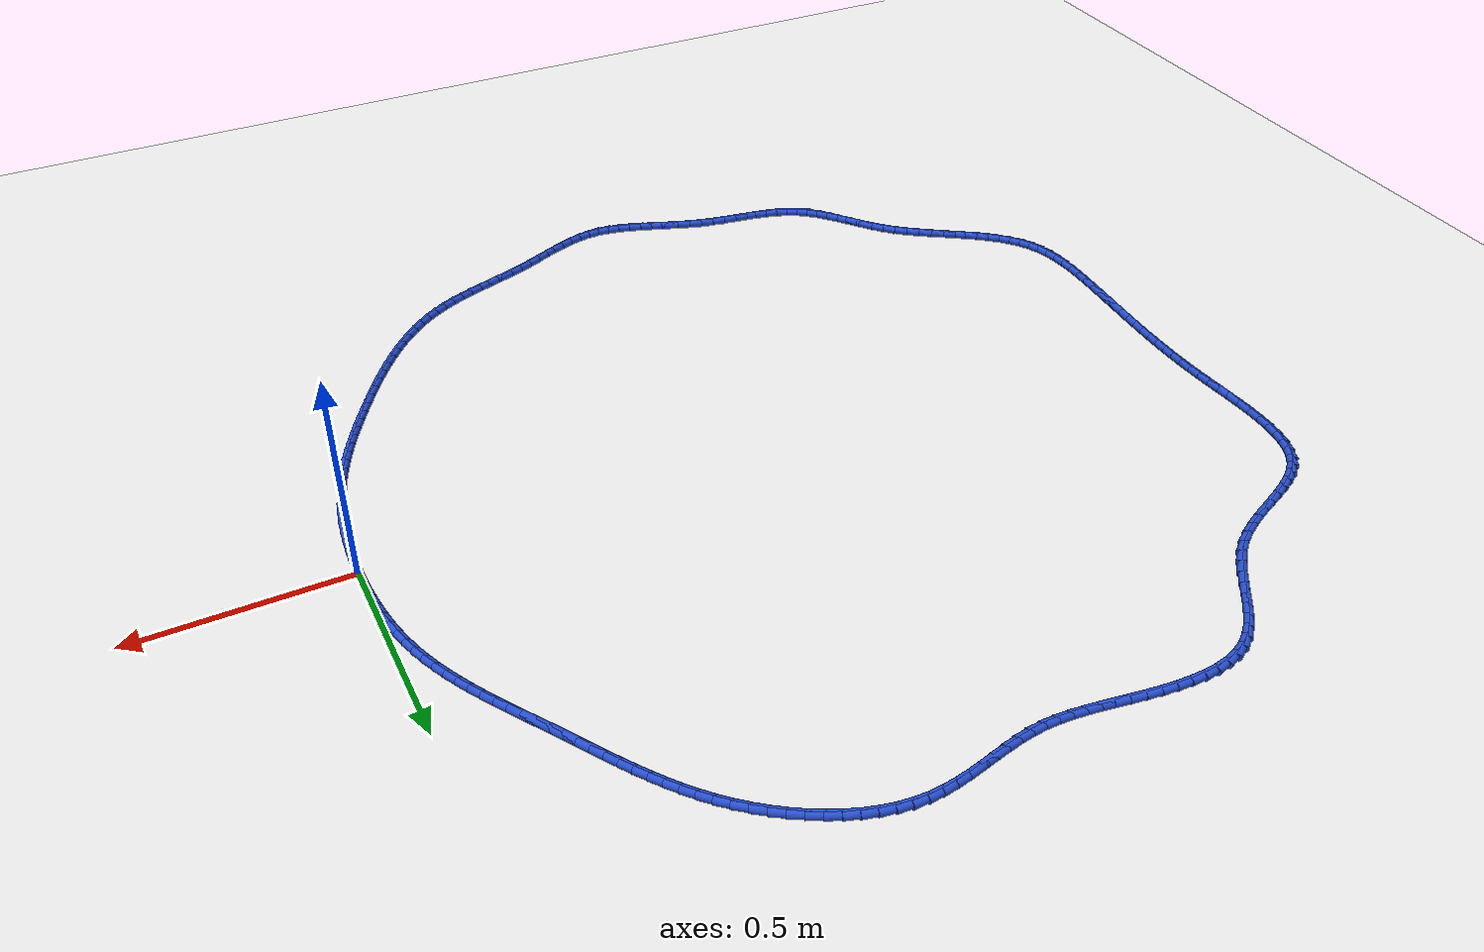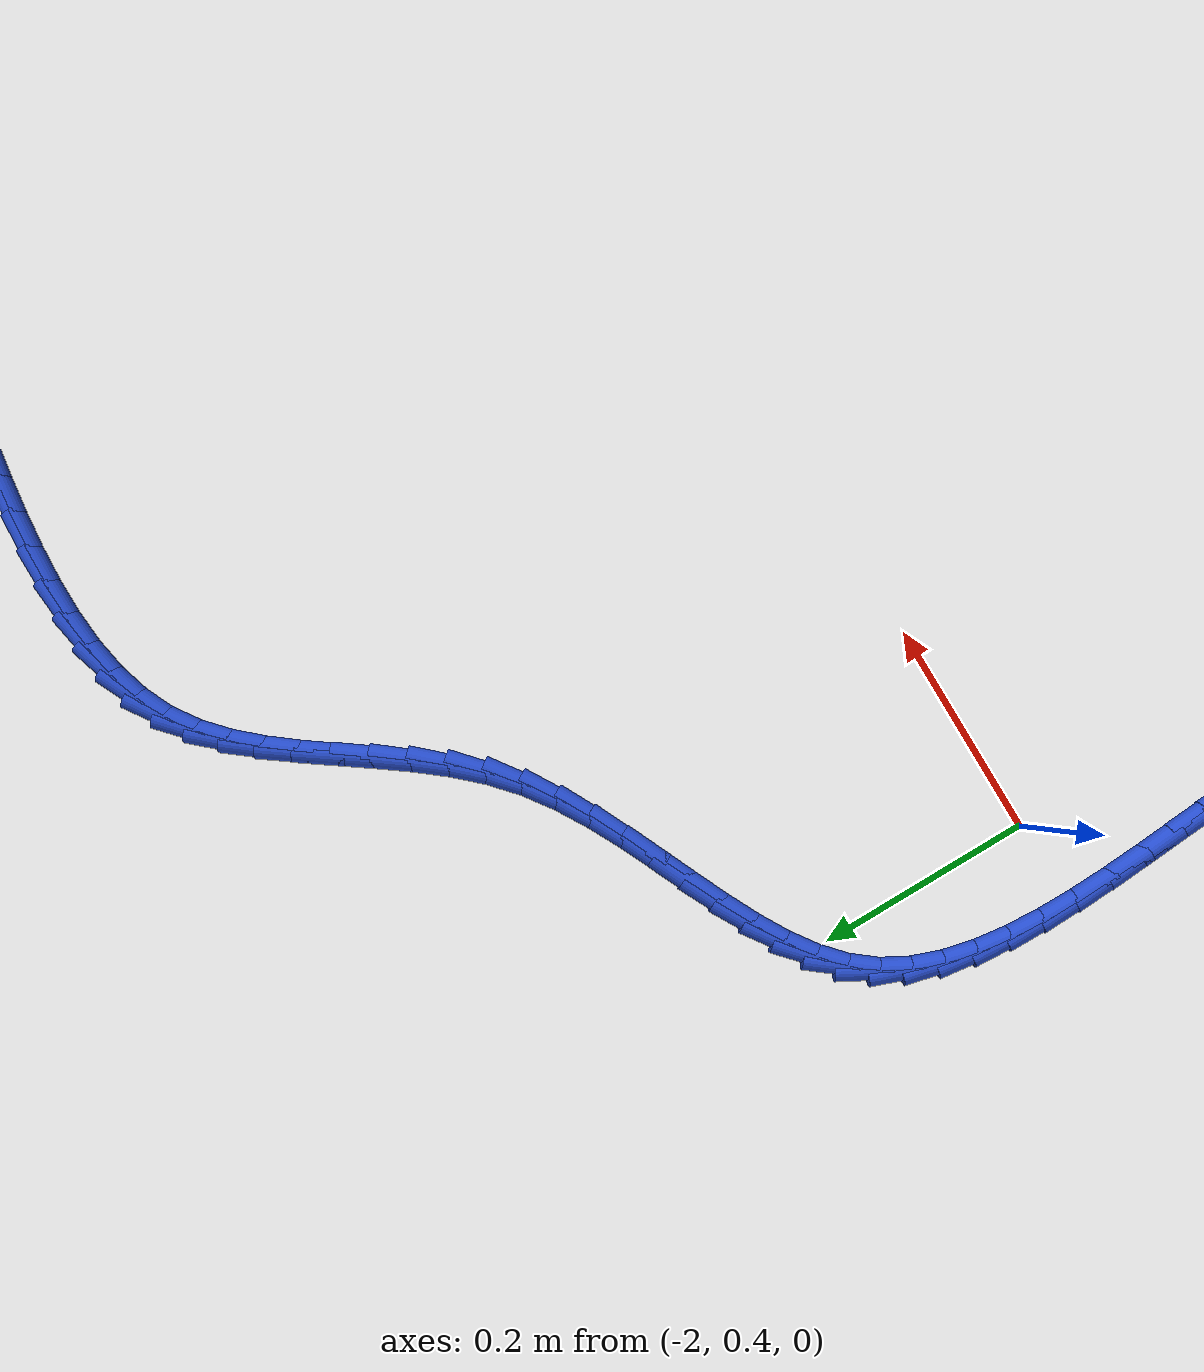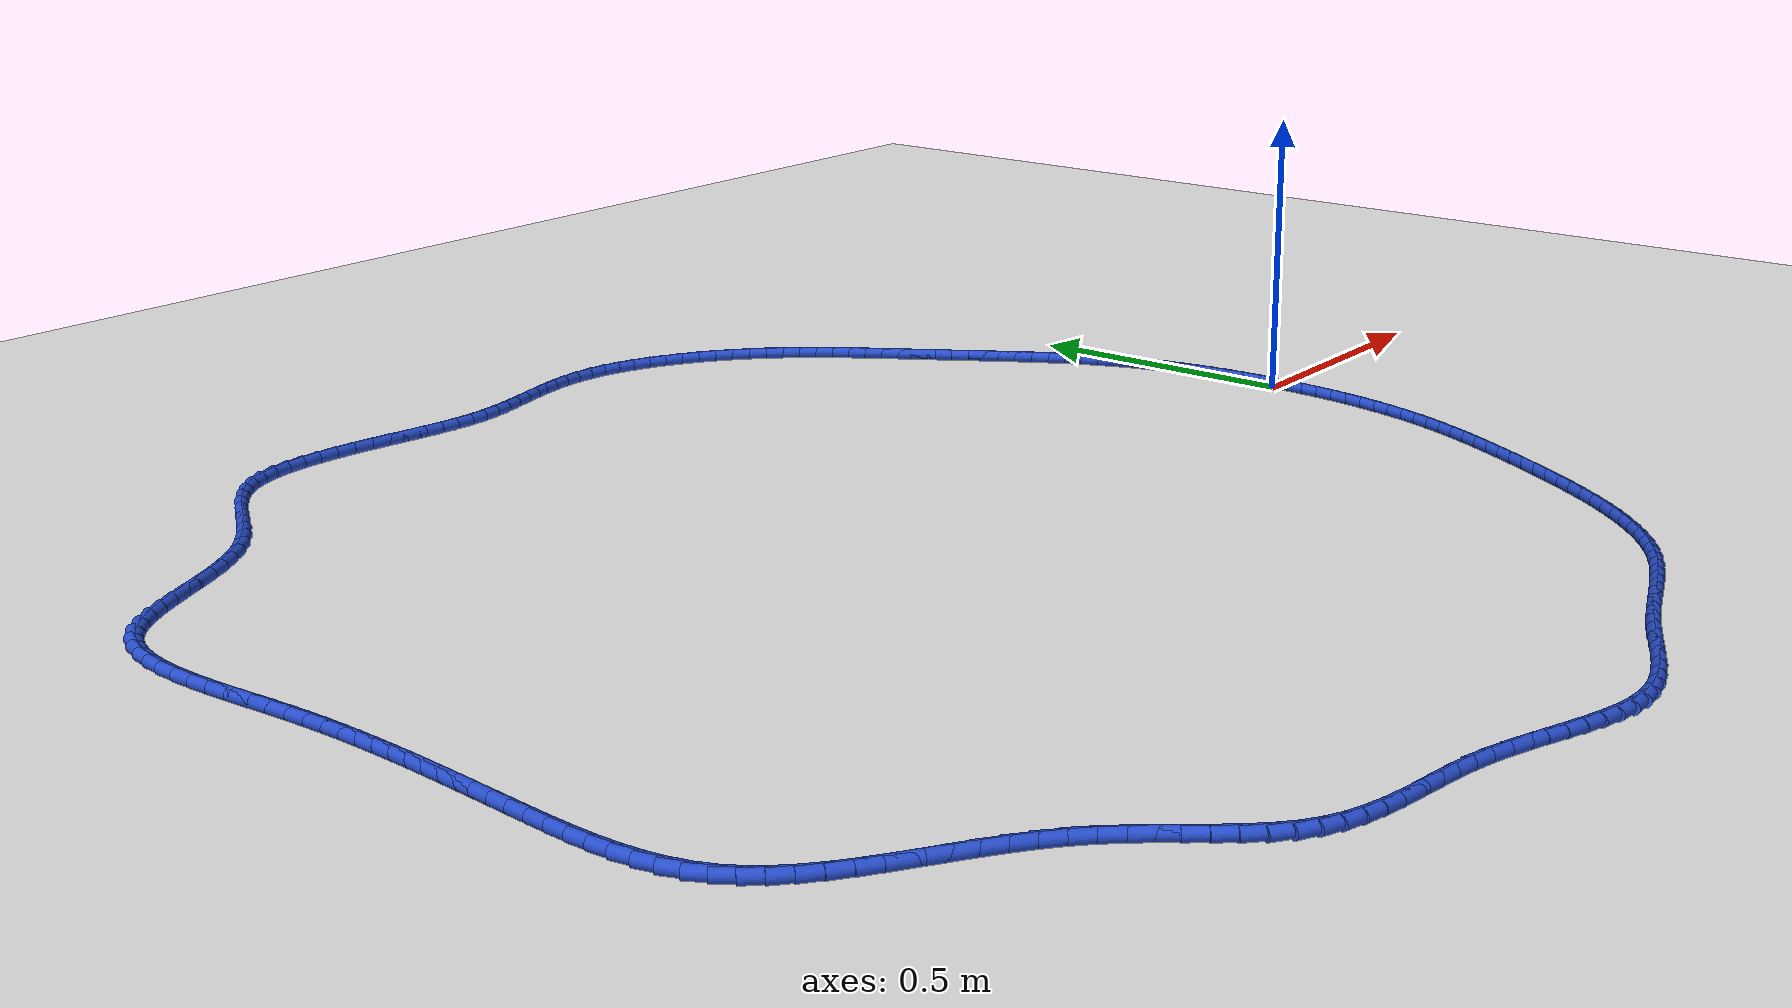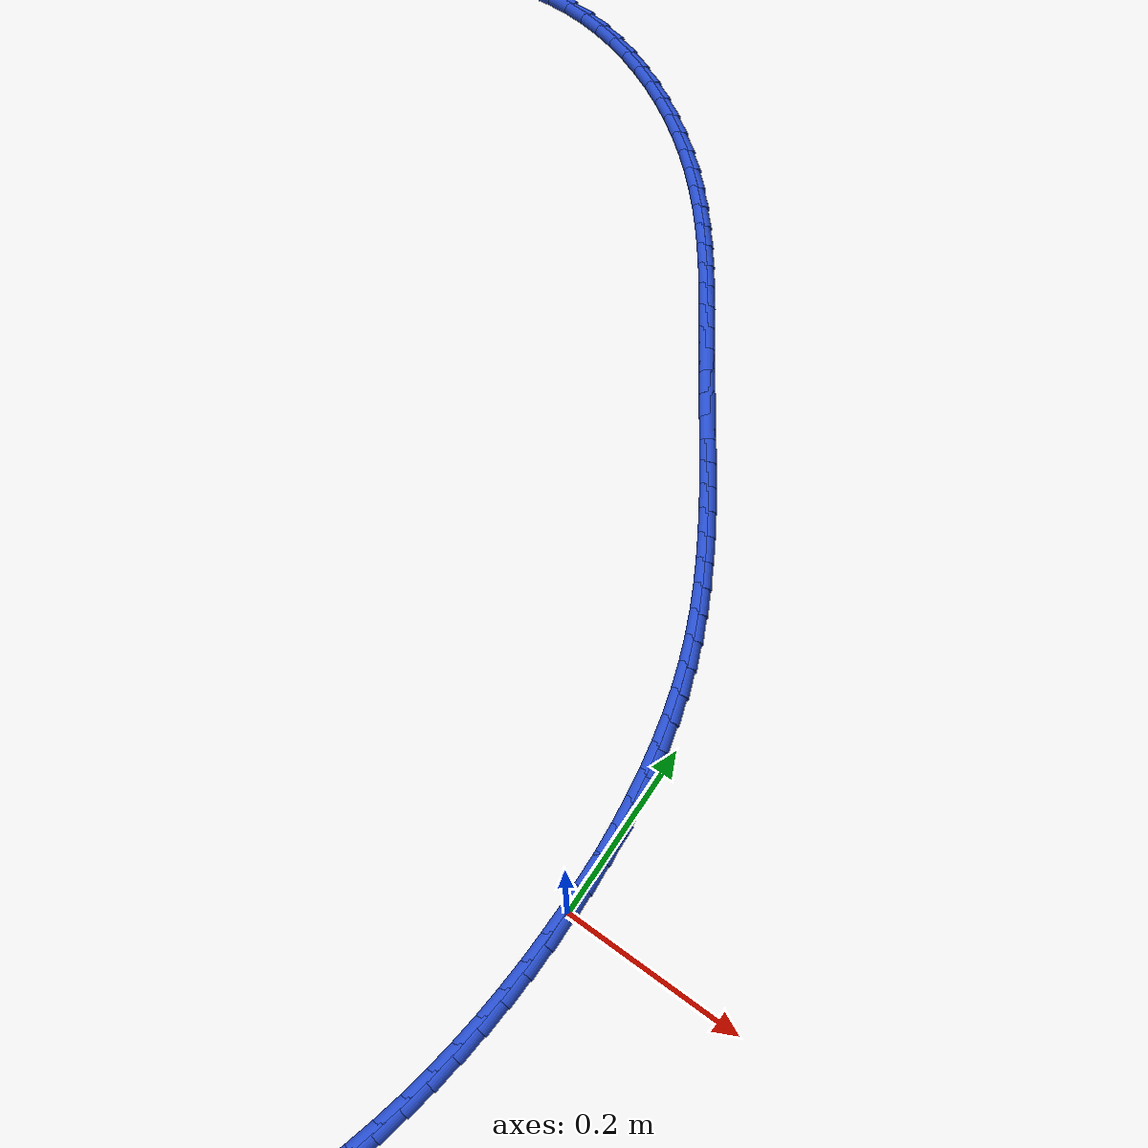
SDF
<sdf version="1.6">
 <world name="default">
  <light name="sun" type="directional">
   <pose>0 0 10 0 -0 0</pose>
   <diffuse>0.8 0.8 0.8 1</diffuse>
   <specular>0.2 0.2 0.2 1</specular>
   <attenuation>
    <range>1000</range>
    <constant>0.9</constant>
    <linear>0.01</linear>
    <quadratic>0.001</quadratic>
   </attenuation>
   <direction>-0.5 0.1 -0.9</direction>
  </light>
  <model name="ground_plane">
   <static>1</static>
   <link name="link">
    <collision name="collision">
     <geometry><plane><normal>0 0 1</normal><size>100 100</size></plane></geometry>
     <surface><friction><ode><mu>100</mu><mu2>50</mu2></ode></friction></surface>
    </collision>
    <visual name="visual">
     <cast_shadows>0</cast_shadows>
     <geometry><plane><normal>0 0 1</normal><size>100 100</size></plane></geometry>
     <material>
      <script><uri>file://media/materials/scripts/gazebo.material</uri><name>Gazebo/WhiteGlow</name></script>
     </material>
    </visual>
   </link>
  </model>
  <gravity>0 0 -9.8</gravity>
  <magnetic_field>6e-06 2.3e-05 -4.2e-05</magnetic_field>
  <atmosphere type="adiabatic"/>
  <physics name="default_physics" default="0" type="ode">
   <max_step_size>0.001</max_step_size>
   <real_time_factor>1</real_time_factor>
   <real_time_update_rate>1000</real_time_update_rate>
  </physics>
  <scene><ambient>0.4 0.4 0.4 1</ambient><background>0.7 0.7 0.7 1</background><shadows>1</shadows></scene>
  <spherical_coordinates>
   <surface_model>EARTH_WGS84</surface_model>
   <latitude_deg>0</latitude_deg>
   <longitude_deg>0</longitude_deg>
   <elevation>0</elevation>
   <heading_deg>0</heading_deg>
  </spherical_coordinates>
  <model name="line">
   <link name="link_0">
    <pose>-8.673617379884035e-18 6.938893903907228e-18 0.01 0 1.57 -1.5631943589973318</pose>
    <collision name="collision">
     <geometry><cylinder><radius>0.01</radius><length>0.08</length></cylinder></geometry>
    </collision>
    <visual name="visual">
     <material>
      <script><name>Gazebo/Blue</name><uri>file://media/materials/scripts/gazebo.material</uri></script>
     </material>
     <geometry><cylinder><radius>0.01</radius><length>0.08</length></cylinder></geometry>
    </visual>
   </link>
   <link name="link_1">
    <pose>-0.00024784472184227464 0.03260207805600657 0.01 0 1.57 -1.533790845903109</pose>
    <collision name="collision">
     <geometry><cylinder><radius>0.01</radius><length>0.08</length></cylinder></geometry>
    </collision>
    <visual name="visual">
     <material>
      <script><name>Gazebo/Blue</name><uri>file://media/materials/scripts/gazebo.material</uri></script>
     </material>
     <geometry><cylinder><radius>0.01</radius><length>0.08</length></cylinder></geometry>
    </visual>
   </link>
   <link name="link_2">
    <pose>-0.0014533980365739327 0.065164902218467 0.01 0 1.57 -1.5024519334454958</pose>
    <collision name="collision">
     <geometry><cylinder><radius>0.01</radius><length>0.08</length></cylinder></geometry>
    </collision>
    <visual name="visual">
     <material>
      <script><name>Gazebo/Blue</name><uri>file://media/materials/scripts/gazebo.material</uri></script>
     </material>
     <geometry><cylinder><radius>0.01</radius><length>0.08</length></cylinder></geometry>
    </visual>
   </link>
   <link name="link_3">
    <pose>-0.0036753420684664316 0.09762525940442635 0.01 0 1.57 -1.4690571654817277</pose>
    <collision name="collision">
     <geometry><cylinder><radius>0.01</radius><length>0.08</length></cylinder></geometry>
    </collision>
    <visual name="visual">
     <material>
      <script><name>Gazebo/Blue</name><uri>file://media/materials/scripts/gazebo.material</uri></script>
     </material>
     <geometry><cylinder><radius>0.01</radius><length>0.08</length></cylinder></geometry>
    </visual>
   </link>
   <link name="link_4">
    <pose>-0.006972358941791235 0.12991993653092962 0.01 0 1.57 -1.4334882361334793</pose>
    <collision name="collision">
     <geometry><cylinder><radius>0.01</radius><length>0.08</length></cylinder></geometry>
    </collision>
    <visual name="visual">
     <material>
      <script><name>Gazebo/Blue</name><uri>file://media/materials/scripts/gazebo.material</uri></script>
     </material>
     <geometry><cylinder><radius>0.01</radius><length>0.08</length></cylinder></geometry>
    </visual>
   </link>
   <link name="link_5">
    <pose>-0.0114031307808198 0.16198572051502183 0.01 0 1.57 -1.395633090768564</pose>
    <collision name="collision">
     <geometry><cylinder><radius>0.01</radius><length>0.08</length></cylinder></geometry>
    </collision>
    <visual name="visual">
     <material>
      <script><name>Gazebo/Blue</name><uri>file://media/materials/scripts/gazebo.material</uri></script>
     </material>
     <geometry><cylinder><radius>0.01</radius><length>0.08</length></cylinder></geometry>
    </visual>
   </link>
   <link name="link_6">
    <pose>-0.017026339709823587 0.1937593982737481 0.01 0 1.57 -1.355391174735926</pose>
    <collision name="collision">
     <geometry><cylinder><radius>0.01</radius><length>0.08</length></cylinder></geometry>
    </collision>
    <visual name="visual">
     <material>
      <script><name>Gazebo/Blue</name><uri>file://media/materials/scripts/gazebo.material</uri></script>
     </material>
     <geometry><cylinder><radius>0.01</radius><length>0.08</length></cylinder></geometry>
    </visual>
   </link>
   <link name="link_7">
    <pose>-0.023900667853074056 0.22517775672415336 0.01 0 1.57 -1.3126799209108013</pose>
    <collision name="collision">
     <geometry><cylinder><radius>0.01</radius><length>0.08</length></cylinder></geometry>
    </collision>
    <visual name="visual">
     <material>
      <script><name>Gazebo/Blue</name><uri>file://media/materials/scripts/gazebo.material</uri></script>
     </material>
     <geometry><cylinder><radius>0.01</radius><length>0.08</length></cylinder></geometry>
    </visual>
   </link>
   <link name="link_8">
    <pose>-0.03208479733484265 0.2561775827832827 0.01 0 1.57 -1.2674424665983375</pose>
    <collision name="collision">
     <geometry><cylinder><radius>0.01</radius><length>0.08</length></cylinder></geometry>
    </collision>
    <visual name="visual">
     <material>
      <script><name>Gazebo/Blue</name><uri>file://media/materials/scripts/gazebo.material</uri></script>
     </material>
     <geometry><cylinder><radius>0.01</radius><length>0.08</length></cylinder></geometry>
    </visual>
   </link>
   <link name="link_9">
    <pose>-0.04163741027940083 0.286695663368181 0.01 0 1.57 -1.2201450502456008</pose>
    <collision name="collision">
     <geometry><cylinder><radius>0.01</radius><length>0.08</length></cylinder></geometry>
    </collision>
    <visual name="visual">
     <material>
      <script><name>Gazebo/Blue</name><uri>file://media/materials/scripts/gazebo.material</uri></script>
     </material>
     <geometry><cylinder><radius>0.01</radius><length>0.08</length></cylinder></geometry>
    </visual>
   </link>
   <link name="link_10">
    <pose>-0.052603454218247386 0.31667664067899987 0.01 0 1.57 -1.175355784121566</pose>
    <collision name="collision">
     <geometry><cylinder><radius>0.01</radius><length>0.08</length></cylinder></geometry>
    </collision>
    <visual name="visual">
     <material>
      <script><name>Gazebo/Blue</name><uri>file://media/materials/scripts/gazebo.material</uri></script>
     </material>
     <geometry><cylinder><radius>0.01</radius><length>0.08</length></cylinder></geometry>
    </visual>
   </link>
   <link name="link_11">
    <pose>-0.06490129482653313 0.346137553406577 0.01 0 1.57 -1.1356481326888397</pose>
    <collision name="collision">
     <geometry><cylinder><radius>0.01</radius><length>0.08</length></cylinder></geometry>
    </collision>
    <visual name="visual">
     <material>
      <script><name>Gazebo/Blue</name><uri>file://media/materials/scripts/gazebo.material</uri></script>
     </material>
     <geometry><cylinder><radius>0.01</radius><length>0.08</length></cylinder></geometry>
    </visual>
   </link>
   <link name="link_12">
    <pose>-0.0783810119978711 0.37513449521447456 0.01 0 1.57 -1.1011148195272438</pose>
    <collision name="collision">
     <geometry><cylinder><radius>0.01</radius><length>0.08</length></cylinder></geometry>
    </collision>
    <visual name="visual">
     <material>
      <script><name>Gazebo/Blue</name><uri>file://media/materials/scripts/gazebo.material</uri></script>
     </material>
     <geometry><cylinder><radius>0.01</radius><length>0.08</length></cylinder></geometry>
    </visual>
   </link>
   <link name="link_13">
    <pose>-0.09289202157249465 0.4037239395610827 0.01 0 1.57 -1.0717514270232071</pose>
    <collision name="collision">
     <geometry><cylinder><radius>0.01</radius><length>0.08</length></cylinder></geometry>
    </collision>
    <visual name="visual">
     <material>
      <script><name>Gazebo/Blue</name><uri>file://media/materials/scripts/gazebo.material</uri></script>
     </material>
     <geometry><cylinder><radius>0.01</radius><length>0.08</length></cylinder></geometry>
    </visual>
   </link>
   <link name="link_14">
    <pose>-0.10828373939063721 0.43196235990479137 0.01 0 1.57 -1.0475078406975615</pose>
    <collision name="collision">
     <geometry><cylinder><radius>0.01</radius><length>0.08</length></cylinder></geometry>
    </collision>
    <visual name="visual">
     <material>
      <script><name>Gazebo/Blue</name><uri>file://media/materials/scripts/gazebo.material</uri></script>
     </material>
     <geometry><cylinder><radius>0.01</radius><length>0.08</length></cylinder></geometry>
    </visual>
   </link>
   <link name="link_15">
    <pose>-0.1244055812925321 0.4599062297039905 0.01 0 1.57 -1.0283118102689512</pose>
    <collision name="collision">
     <geometry><cylinder><radius>0.01</radius><length>0.08</length></cylinder></geometry>
    </collision>
    <visual name="visual">
     <material>
      <script><name>Gazebo/Blue</name><uri>file://media/materials/scripts/gazebo.material</uri></script>
     </material>
     <geometry><cylinder><radius>0.01</radius><length>0.08</length></cylinder></geometry>
    </visual>
   </link>
   <link name="link_16">
    <pose>-0.14110696311841273 0.48761202241706997 0.01 0 1.57 -1.0140876542201926</pose>
    <collision name="collision">
     <geometry><cylinder><radius>0.01</radius><length>0.08</length></cylinder></geometry>
    </collision>
    <visual name="visual">
     <material>
      <script><name>Gazebo/Blue</name><uri>file://media/materials/scripts/gazebo.material</uri></script>
     </material>
     <geometry><cylinder><radius>0.01</radius><length>0.08</length></cylinder></geometry>
    </visual>
   </link>
   <link name="link_17">
    <pose>-0.15823730070851247 0.51513621150242 0.01 0 1.57 -1.0047702653075612</pose>
    <collision name="collision">
     <geometry><cylinder><radius>0.01</radius><length>0.08</length></cylinder></geometry>
    </collision>
    <visual name="visual">
     <material>
      <script><name>Gazebo/Blue</name><uri>file://media/materials/scripts/gazebo.material</uri></script>
     </material>
     <geometry><cylinder><radius>0.01</radius><length>0.08</length></cylinder></geometry>
    </visual>
   </link>
   <link name="link_18">
    <pose>-0.17564600990306484 0.5425352704184305 0.01 0 1.57 -1.0003149174076857</pose>
    <collision name="collision">
     <geometry><cylinder><radius>0.01</radius><length>0.08</length></cylinder></geometry>
    </collision>
    <visual name="visual">
     <material>
      <script><name>Gazebo/Blue</name><uri>file://media/materials/scripts/gazebo.material</uri></script>
     </material>
     <geometry><cylinder><radius>0.01</radius><length>0.08</length></cylinder></geometry>
    </visual>
   </link>
   <link name="link_19">
    <pose>-0.1931825065423031 0.5698656726234913 0.01 0 1.57 -1.000703427991057</pose>
    <collision name="collision">
     <geometry><cylinder><radius>0.01</radius><length>0.08</length></cylinder></geometry>
    </collision>
    <visual name="visual">
     <material>
      <script><name>Gazebo/Blue</name><uri>file://media/materials/scripts/gazebo.material</uri></script>
     </material>
     <geometry><cylinder><radius>0.01</radius><length>0.08</length></cylinder></geometry>
    </visual>
   </link>
   <link name="link_20">
    <pose>-0.21069620646646062 0.5971838915759925 0.01 0 1.57 -1.0058750031840649</pose>
    <collision name="collision">
     <geometry><cylinder><radius>0.01</radius><length>0.08</length></cylinder></geometry>
    </collision>
    <visual name="visual">
     <material>
      <script><name>Gazebo/Blue</name><uri>file://media/materials/scripts/gazebo.material</uri></script>
     </material>
     <geometry><cylinder><radius>0.01</radius><length>0.08</length></cylinder></geometry>
    </visual>
   </link>
   <link name="link_21">
    <pose>-0.22803864262422394 0.6245453779863667 0.01 0 1.57 -1.0118614931017058</pose>
    <collision name="collision">
     <geometry><cylinder><radius>0.01</radius><length>0.08</length></cylinder></geometry>
    </collision>
    <visual name="visual">
     <material>
      <script><name>Gazebo/Blue</name><uri>file://media/materials/scripts/gazebo.material</uri></script>
     </material>
     <geometry><cylinder><radius>0.01</radius><length>0.08</length></cylinder></geometry>
    </visual>
   </link>
   <link name="link_22">
    <pose>-0.24517864398886402 0.6519489183590288 0.01 0 1.57 -1.0126347728544314</pose>
    <collision name="collision">
     <geometry><cylinder><radius>0.01</radius><length>0.08</length></cylinder></geometry>
    </collision>
    <visual name="visual">
     <material>
      <script><name>Gazebo/Blue</name><uri>file://media/materials/scripts/gazebo.material</uri></script>
     </material>
     <geometry><cylinder><radius>0.01</radius><length>0.08</length></cylinder></geometry>
    </visual>
   </link>
   <link name="link_23">
    <pose>-0.2622614636988771 0.6793080709455147 0.01 0 1.57 -1.0076622553800159</pose>
    <collision name="collision">
     <geometry><cylinder><radius>0.01</radius><length>0.08</length></cylinder></geometry>
    </collision>
    <visual name="visual">
     <material>
      <script><name>Gazebo/Blue</name><uri>file://media/materials/scripts/gazebo.material</uri></script>
     </material>
     <geometry><cylinder><radius>0.01</radius><length>0.08</length></cylinder></geometry>
    </visual>
   </link>
   <link name="link_24">
    <pose>-0.2794469188122245 0.706529358354543 0.01 0 1.57 -0.9969140273976459</pose>
    <collision name="collision">
     <geometry><cylinder><radius>0.01</radius><length>0.08</length></cylinder></geometry>
    </collision>
    <visual name="visual">
     <material>
      <script><name>Gazebo/Blue</name><uri>file://media/materials/scripts/gazebo.material</uri></script>
     </material>
     <geometry><cylinder><radius>0.01</radius><length>0.08</length></cylinder></geometry>
    </visual>
   </link>
   <link name="link_25">
    <pose>-0.29689482638686754 0.7335193031948317 0.01 0 1.57 -0.9803719907704949</pose>
    <collision name="collision">
     <geometry><cylinder><radius>0.01</radius><length>0.08</length></cylinder></geometry>
    </collision>
    <visual name="visual">
     <material>
      <script><name>Gazebo/Blue</name><uri>file://media/materials/scripts/gazebo.material</uri></script>
     </material>
     <geometry><cylinder><radius>0.01</radius><length>0.08</length></cylinder></geometry>
    </visual>
   </link>
   <link name="link_26">
    <pose>-0.31476500348076714 0.7601844280750986 0.01 0 1.57 -0.9580408075878378</pose>
    <collision name="collision">
     <geometry><cylinder><radius>0.01</radius><length>0.08</length></cylinder></geometry>
    </collision>
    <visual name="visual">
     <material>
      <script><name>Gazebo/Blue</name><uri>file://media/materials/scripts/gazebo.material</uri></script>
     </material>
     <geometry><cylinder><radius>0.01</radius><length>0.08</length></cylinder></geometry>
    </visual>
   </link>
   <link name="link_27">
    <pose>-0.3332172671518848 0.7864312556040624 0.01 0 1.57 -0.9299645481422498</pose>
    <collision name="collision">
     <geometry><cylinder><radius>0.01</radius><length>0.08</length></cylinder></geometry>
    </collision>
    <visual name="visual">
     <material>
      <script><name>Gazebo/Blue</name><uri>file://media/materials/scripts/gazebo.material</uri></script>
     </material>
     <geometry><cylinder><radius>0.01</radius><length>0.08</length></cylinder></geometry>
    </visual>
   </link>
   <link name="link_28">
    <pose>-0.3524114344581818 0.812166308390441 0.01 0 1.57 -0.8962483764619484</pose>
    <collision name="collision">
     <geometry><cylinder><radius>0.01</radius><length>0.08</length></cylinder></geometry>
    </collision>
    <visual name="visual">
     <material>
      <script><name>Gazebo/Blue</name><uri>file://media/materials/scripts/gazebo.material</uri></script>
     </material>
     <geometry><cylinder><radius>0.01</radius><length>0.08</length></cylinder></geometry>
    </visual>
   </link>
   <link name="link_29">
    <pose>-0.3725073224576191 0.8372961090429525 0.01 0 1.57 -0.8570837008588502</pose>
    <collision name="collision">
     <geometry><cylinder><radius>0.01</radius><length>0.08</length></cylinder></geometry>
    </collision>
    <visual name="visual">
     <material>
      <script><name>Gazebo/Blue</name><uri>file://media/materials/scripts/gazebo.material</uri></script>
     </material>
     <geometry><cylinder><radius>0.01</radius><length>0.08</length></cylinder></geometry>
    </visual>
   </link>
   <link name="link_30">
    <pose>-0.393664748208158 0.8617271801703149 0.01 0 1.57 -0.8127739419498019</pose>
    <collision name="collision">
     <geometry><cylinder><radius>0.01</radius><length>0.08</length></cylinder></geometry>
    </collision>
    <visual name="visual">
     <material>
      <script><name>Gazebo/Blue</name><uri>file://media/materials/scripts/gazebo.material</uri></script>
     </material>
     <geometry><cylinder><radius>0.01</radius><length>0.08</length></cylinder></geometry>
    </visual>
   </link>
   <link name="link_31">
    <pose>-0.4160435287677597 0.8853660443812466 0.01 0 1.57 -0.7638232330316025</pose>
    <collision name="collision">
     <geometry><cylinder><radius>0.01</radius><length>0.08</length></cylinder></geometry>
    </collision>
    <visual name="visual">
     <material>
      <script><name>Gazebo/Blue</name><uri>file://media/materials/scripts/gazebo.material</uri></script>
     </material>
     <geometry><cylinder><radius>0.01</radius><length>0.08</length></cylinder></geometry>
    </visual>
   </link>
   <link name="link_32">
    <pose>-0.43979872626941885 0.908117703966737 0.01 0 1.57 -0.7124274869079873</pose>
    <collision name="collision">
     <geometry><cylinder><radius>0.01</radius><length>0.08</length></cylinder></geometry>
    </collision>
    <visual name="visual">
     <material>
      <script><name>Gazebo/Blue</name><uri>file://media/materials/scripts/gazebo.material</uri></script>
     </material>
     <geometry><cylinder><radius>0.01</radius><length>0.08</length></cylinder></geometry>
    </visual>
   </link>
   <link name="link_33">
    <pose>-0.4649528317305743 0.9298447735421119 0.01 0 1.57 -0.6601596125488771</pose>
    <collision name="collision">
     <geometry><cylinder><radius>0.01</radius><length>0.08</length></cylinder></geometry>
    </collision>
    <visual name="visual">
     <material>
      <script><name>Gazebo/Blue</name><uri>file://media/materials/scripts/gazebo.material</uri></script>
     </material>
     <geometry><cylinder><radius>0.01</radius><length>0.08</length></cylinder></geometry>
    </visual>
   </link>
   <link name="link_34">
    <pose>-0.4913814258037381 0.9503628952817245 0.01 0 1.57 -0.6063959061464046</pose>
    <collision name="collision">
     <geometry><cylinder><radius>0.01</radius><length>0.08</length></cylinder></geometry>
    </collision>
    <visual name="visual">
     <material>
      <script><name>Gazebo/Blue</name><uri>file://media/materials/scripts/gazebo.material</uri></script>
     </material>
     <geometry><cylinder><radius>0.01</radius><length>0.08</length></cylinder></geometry>
    </visual>
   </link>
   <link name="link_35">
    <pose>-0.5189524568804732 0.9694852710560934 0.01 0 1.57 -0.5504173423679374</pose>
    <collision name="collision">
     <geometry><cylinder><radius>0.01</radius><length>0.08</length></cylinder></geometry>
    </collision>
    <visual name="visual">
     <material>
      <script><name>Gazebo/Blue</name><uri>file://media/materials/scripts/gazebo.material</uri></script>
     </material>
     <geometry><cylinder><radius>0.01</radius><length>0.08</length></cylinder></geometry>
    </visual>
   </link>
   <link name="link_36">
    <pose>-0.5475338733523413 0.9870251027357363 0.01 0 1.57 -0.4915052944230036</pose>
    <collision name="collision">
     <geometry><cylinder><radius>0.01</radius><length>0.08</length></cylinder></geometry>
    </collision>
    <visual name="visual">
     <material>
      <script><name>Gazebo/Blue</name><uri>file://media/materials/scripts/gazebo.material</uri></script>
     </material>
     <geometry><cylinder><radius>0.01</radius><length>0.08</length></cylinder></geometry>
    </visual>
   </link>
   <link name="link_37">
    <pose>-0.5769936236109053 1.0027955921911713 0.01 0 1.57 -0.42893895141502464</pose>
    <collision name="collision">
     <geometry><cylinder><radius>0.01</radius><length>0.08</length></cylinder></geometry>
    </collision>
    <visual name="visual">
     <material>
      <script><name>Gazebo/Blue</name><uri>file://media/materials/scripts/gazebo.material</uri></script>
     </material>
     <geometry><cylinder><radius>0.01</radius><length>0.08</length></cylinder></geometry>
    </visual>
   </link>
   <link name="link_38">
    <pose>-0.6071996560477273 1.0166099412929166 0.01 0 1.57 -0.3620042259327489</pose>
    <collision name="collision">
     <geometry><cylinder><radius>0.01</radius><length>0.08</length></cylinder></geometry>
    </collision>
    <visual name="visual">
     <material>
      <script><name>Gazebo/Blue</name><uri>file://media/materials/scripts/gazebo.material</uri></script>
     </material>
     <geometry><cylinder><radius>0.01</radius><length>0.08</length></cylinder></geometry>
    </visual>
   </link>
   <link name="link_39">
    <pose>-0.6380199190543697 1.0282813519114902 0.01 0 1.57 -0.2900183358659372</pose>
    <collision name="collision">
     <geometry><cylinder><radius>0.01</radius><length>0.08</length></cylinder></geometry>
    </collision>
    <visual name="visual">
     <material>
      <script><name>Gazebo/Blue</name><uri>file://media/materials/scripts/gazebo.material</uri></script>
     </material>
     <geometry><cylinder><radius>0.01</radius><length>0.08</length></cylinder></geometry>
    </visual>
   </link>
   <link name="link_40">
    <pose>-0.6693223610223952 1.0376230259174106 0.01 0 1.57 -0.21237509941672514</pose>
    <collision name="collision">
     <geometry><cylinder><radius>0.01</radius><length>0.08</length></cylinder></geometry>
    </collision>
    <visual name="visual">
     <material>
      <script><name>Gazebo/Blue</name><uri>file://media/materials/scripts/gazebo.material</uri></script>
     </material>
     <geometry><cylinder><radius>0.01</radius><length>0.08</length></cylinder></geometry>
    </visual>
   </link>
   <link name="link_41">
    <pose>-0.7009749303433658 1.0444481651811957 0.01 0 1.57 -0.1286153377310343</pose>
    <collision name="collision">
     <geometry><cylinder><radius>0.01</radius><length>0.08</length></cylinder></geometry>
    </collision>
    <visual name="visual">
     <material>
      <script><name>Gazebo/Blue</name><uri>file://media/materials/scripts/gazebo.material</uri></script>
     </material>
     <geometry><cylinder><radius>0.01</radius><length>0.08</length></cylinder></geometry>
    </visual>
   </link>
   <link name="link_42">
    <pose>-0.7328455754088439 1.0485699715733632 0.01 0 1.57 -0.038522977664698574</pose>
    <collision name="collision">
     <geometry><cylinder><radius>0.01</radius><length>0.08</length></cylinder></geometry>
    </collision>
    <visual name="visual">
     <material>
      <script><name>Gazebo/Blue</name><uri>file://media/materials/scripts/gazebo.material</uri></script>
     </material>
     <geometry><cylinder><radius>0.01</radius><length>0.08</length></cylinder></geometry>
    </visual>
   </link>
   <link name="link_43">
    <pose>-0.7648022446103924 1.0498016469644322 0.01 0 1.57 0.05433180176027462</pose>
    <collision name="collision">
     <geometry><cylinder><radius>0.01</radius><length>0.08</length></cylinder></geometry>
    </collision>
    <visual name="visual">
     <material>
      <script><name>Gazebo/Blue</name><uri>file://media/materials/scripts/gazebo.material</uri></script>
     </material>
     <geometry><cylinder><radius>0.01</radius><length>0.08</length></cylinder></geometry>
    </visual>
   </link>
   <link name="link_44">
    <pose>-0.796729353519501 1.0480652807237087 0.01 0 1.57 0.13166742885493868</pose>
    <collision name="collision">
     <geometry><cylinder><radius>0.01</radius><length>0.08</length></cylinder></geometry>
    </collision>
    <visual name="visual">
     <material>
      <script><name>Gazebo/Blue</name><uri>file://media/materials/scripts/gazebo.material</uri></script>
     </material>
     <geometry><cylinder><radius>0.01</radius><length>0.08</length></cylinder></geometry>
    </visual>
   </link>
   <link name="link_45">
    <pose>-0.8285963188274681 1.0438450232030496 0.01 0 1.57 0.187655477571221</pose>
    <collision name="collision">
     <geometry><cylinder><radius>0.01</radius><length>0.08</length></cylinder></geometry>
    </collision>
    <visual name="visual">
     <material>
      <script><name>Gazebo/Blue</name><uri>file://media/materials/scripts/gazebo.material</uri></script>
     </material>
     <geometry><cylinder><radius>0.01</radius><length>0.08</length></cylinder></geometry>
    </visual>
   </link>
   <link name="link_46">
    <pose>-0.8603999036841893 1.0378058503413552 0.01 0 1.57 0.22287956981717122</pose>
    <collision name="collision">
     <geometry><cylinder><radius>0.01</radius><length>0.08</length></cylinder></geometry>
    </collision>
    <visual name="visual">
     <material>
      <script><name>Gazebo/Blue</name><uri>file://media/materials/scripts/gazebo.material</uri></script>
     </material>
     <geometry><cylinder><radius>0.01</radius><length>0.08</length></cylinder></geometry>
    </visual>
   </link>
   <link name="link_47">
    <pose>-0.8921368842636005 1.0306128241976285 0.01 0 1.57 0.23798301975057237</pose>
    <collision name="collision">
     <geometry><cylinder><radius>0.01</radius><length>0.08</length></cylinder></geometry>
    </collision>
    <visual name="visual">
     <material>
      <script><name>Gazebo/Blue</name><uri>file://media/materials/scripts/gazebo.material</uri></script>
     </material>
     <geometry><cylinder><radius>0.01</radius><length>0.08</length></cylinder></geometry>
    </visual>
   </link>
   <link name="link_48">
    <pose>-0.9238040367396388 1.0229310068308712 0.01 0 1.57 0.23323815431395195</pose>
    <collision name="collision">
     <geometry><cylinder><radius>0.01</radius><length>0.08</length></cylinder></geometry>
    </collision>
    <visual name="visual">
     <material>
      <script><name>Gazebo/Blue</name><uri>file://media/materials/scripts/gazebo.material</uri></script>
     </material>
     <geometry><cylinder><radius>0.01</radius><length>0.08</length></cylinder></geometry>
    </visual>
   </link>
   <link name="link_49">
    <pose>-0.9553981372862398 1.0154254603000856 0.01 0 1.57 0.20837354650033618</pose>
    <collision name="collision">
     <geometry><cylinder><radius>0.01</radius><length>0.08</length></cylinder></geometry>
    </collision>
    <visual name="visual">
     <material>
      <script><name>Gazebo/Blue</name><uri>file://media/materials/scripts/gazebo.material</uri></script>
     </material>
     <geometry><cylinder><radius>0.01</radius><length>0.08</length></cylinder></geometry>
    </visual>
   </link>
   <link name="link_50">
    <pose>-0.9869159620773402 1.0087612466642735 0.01 0 1.57 0.1626128514162077</pose>
    <collision name="collision">
     <geometry><cylinder><radius>0.01</radius><length>0.08</length></cylinder></geometry>
    </collision>
    <visual name="visual">
     <material>
      <script><name>Gazebo/Blue</name><uri>file://media/materials/scripts/gazebo.material</uri></script>
     </material>
     <geometry><cylinder><radius>0.01</radius><length>0.08</length></cylinder></geometry>
    </visual>
   </link>
   <link name="link_51">
    <pose>-1.018354287286876 1.003603427982437 0.01 0 1.57 0.09518657205054473</pose>
    <collision name="collision">
     <geometry><cylinder><radius>0.01</radius><length>0.08</length></cylinder></geometry>
    </collision>
    <visual name="visual">
     <material>
      <script><name>Gazebo/Blue</name><uri>file://media/materials/scripts/gazebo.material</uri></script>
     </material>
     <geometry><cylinder><radius>0.01</radius><length>0.08</length></cylinder></geometry>
    </visual>
   </link>
   <link name="link_52">
    <pose>-1.0497106885198249 1.0006096725471751 0.01 0 1.57 0.018820083207032594</pose>
    <collision name="collision">
     <geometry><cylinder><radius>0.01</radius><length>0.08</length></cylinder></geometry>
    </collision>
    <visual name="visual">
     <material>
      <script><name>Gazebo/Blue</name><uri>file://media/materials/scripts/gazebo.material</uri></script>
     </material>
     <geometry><cylinder><radius>0.01</radius><length>0.08</length></cylinder></geometry>
    </visual>
   </link>
   <link name="link_53">
    <pose>-1.0810278757135687 1.0000202108818392 0.01 0 1.57 -0.04529241357038745</pose>
    <collision name="collision">
     <geometry><cylinder><radius>0.01</radius><length>0.08</length></cylinder></geometry>
    </collision>
    <visual name="visual">
     <material>
      <script><name>Gazebo/Blue</name><uri>file://media/materials/scripts/gazebo.material</uri></script>
     </material>
     <geometry><cylinder><radius>0.01</radius><length>0.08</length></cylinder></geometry>
    </visual>
   </link>
   <link name="link_54">
    <pose>-1.1124169357157976 1.001442870117793 0.01 0 1.57 -0.09440181729419449</pose>
    <collision name="collision">
     <geometry><cylinder><radius>0.01</radius><length>0.08</length></cylinder></geometry>
    </collision>
    <visual name="visual">
     <material>
      <script><name>Gazebo/Blue</name><uri>file://media/materials/scripts/gazebo.material</uri></script>
     </material>
     <geometry><cylinder><radius>0.01</radius><length>0.08</length></cylinder></geometry>
    </visual>
   </link>
   <link name="link_55">
    <pose>-1.1439946562457157 1.004432751247332 0.01 0 1.57 -0.12826913814941981</pose>
    <collision name="collision">
     <geometry><cylinder><radius>0.01</radius><length>0.08</length></cylinder></geometry>
    </collision>
    <visual name="visual">
     <material>
      <script><name>Gazebo/Blue</name><uri>file://media/materials/scripts/gazebo.material</uri></script>
     </material>
     <geometry><cylinder><radius>0.01</radius><length>0.08</length></cylinder></geometry>
    </visual>
   </link>
   <link name="link_56">
    <pose>-1.1758778250225268 1.008544955262752 0.01 0 1.57 -0.1471886691255853</pose>
    <collision name="collision">
     <geometry><cylinder><radius>0.01</radius><length>0.08</length></cylinder></geometry>
    </collision>
    <visual name="visual">
     <material>
      <script><name>Gazebo/Blue</name><uri>file://media/materials/scripts/gazebo.material</uri></script>
     </material>
     <geometry><cylinder><radius>0.01</radius><length>0.08</length></cylinder></geometry>
    </visual>
   </link>
   <link name="link_57">
    <pose>-1.2081832297654334 1.0133345831563483 0.01 0 1.57 -0.15173204980139357</pose>
    <collision name="collision">
     <geometry><cylinder><radius>0.01</radius><length>0.08</length></cylinder></geometry>
    </collision>
    <visual name="visual">
     <material>
      <script><name>Gazebo/Blue</name><uri>file://media/materials/scripts/gazebo.material</uri></script>
     </material>
     <geometry><cylinder><radius>0.01</radius><length>0.08</length></cylinder></geometry>
    </visual>
   </link>
   <link name="link_58">
    <pose>-1.2410276581936395 1.0183567359204178 0.01 0 1.57 -0.1426028126251293</pose>
    <collision name="collision">
     <geometry><cylinder><radius>0.01</radius><length>0.08</length></cylinder></geometry>
    </collision>
    <visual name="visual">
     <material>
      <script><name>Gazebo/Blue</name><uri>file://media/materials/scripts/gazebo.material</uri></script>
     </material>
     <geometry><cylinder><radius>0.01</radius><length>0.08</length></cylinder></geometry>
    </visual>
   </link>
   <link name="link_59">
    <pose>-1.274527210241311 1.0231665137286856 0.01 0 1.57 -0.12110197321760002</pose>
    <collision name="collision">
     <geometry><cylinder><radius>0.01</radius><length>0.08</length></cylinder></geometry>
    </collision>
    <visual name="visual">
     <material>
      <script><name>Gazebo/Blue</name><uri>file://media/materials/scripts/gazebo.material</uri></script>
     </material>
     <geometry><cylinder><radius>0.01</radius><length>0.08</length></cylinder></geometry>
    </visual>
   </link>
   <link name="link_60">
    <pose>-1.3086472559877511 1.0273188373632838 0.01 0 1.57 -0.08849791112264868</pose>
    <collision name="collision">
     <geometry><cylinder><radius>0.01</radius><length>0.08</length></cylinder></geometry>
    </collision>
    <visual name="visual">
     <material>
      <script><name>Gazebo/Blue</name><uri>file://media/materials/scripts/gazebo.material</uri></script>
     </material>
     <geometry><cylinder><radius>0.01</radius><length>0.08</length></cylinder></geometry>
    </visual>
   </link>
   <link name="link_61">
    <pose>-1.343014418701242 1.0303682244457963 0.01 0 1.57 -0.04386501316778979</pose>
    <collision name="collision">
     <geometry><cylinder><radius>0.01</radius><length>0.08</length></cylinder></geometry>
    </collision>
    <visual name="visual">
     <material>
      <script><name>Gazebo/Blue</name><uri>file://media/materials/scripts/gazebo.material</uri></script>
     </material>
     <geometry><cylinder><radius>0.01</radius><length>0.08</length></cylinder></geometry>
    </visual>
   </link>
   <link name="link_62">
    <pose>-1.3772091050817554 1.0318691375930185 0.01 0 1.57 0.014673344796306026</pose>
    <collision name="collision">
     <geometry><cylinder><radius>0.01</radius><length>0.08</length></cylinder></geometry>
    </collision>
    <visual name="visual">
     <material>
      <script><name>Gazebo/Blue</name><uri>file://media/materials/scripts/gazebo.material</uri></script>
     </material>
     <geometry><cylinder><radius>0.01</radius><length>0.08</length></cylinder></geometry>
    </visual>
   </link>
   <link name="link_63">
    <pose>-1.4108117218292626 1.0313760394217457 0.01 0 1.57 0.08974176962137523</pose>
    <collision name="collision">
     <geometry><cylinder><radius>0.01</radius><length>0.08</length></cylinder></geometry>
    </collision>
    <visual name="visual">
     <material>
      <script><name>Gazebo/Blue</name><uri>file://media/materials/scripts/gazebo.material</uri></script>
     </material>
     <geometry><cylinder><radius>0.01</radius><length>0.08</length></cylinder></geometry>
    </visual>
   </link>
   <link name="link_64">
    <pose>-1.443402675643733 1.0284433925487728 0.01 0 1.57 0.184581750508797</pose>
    <collision name="collision">
     <geometry><cylinder><radius>0.01</radius><length>0.08</length></cylinder></geometry>
    </collision>
    <visual name="visual">
     <material>
      <script><name>Gazebo/Blue</name><uri>file://media/materials/scripts/gazebo.material</uri></script>
     </material>
     <geometry><cylinder><radius>0.01</radius><length>0.08</length></cylinder></geometry>
    </visual>
   </link>
   <link name="link_65">
    <pose>-1.4745623732251385 1.022625659590895 0.01 0 1.57 0.30255352402661145</pose>
    <collision name="collision">
     <geometry><cylinder><radius>0.01</radius><length>0.08</length></cylinder></geometry>
    </collision>
    <visual name="visual">
     <material>
      <script><name>Gazebo/Blue</name><uri>file://media/materials/scripts/gazebo.material</uri></script>
     </material>
     <geometry><cylinder><radius>0.01</radius><length>0.08</length></cylinder></geometry>
    </visual>
   </link>
   <link name="link_66">
    <pose>-1.5038712212734502 1.0134773031649074 0.01 0 1.57 0.44589802409268076</pose>
    <collision name="collision">
     <geometry><cylinder><radius>0.01</radius><length>0.08</length></cylinder></geometry>
    </collision>
    <visual name="visual">
     <material>
      <script><name>Gazebo/Blue</name><uri>file://media/materials/scripts/gazebo.material</uri></script>
     </material>
     <geometry><cylinder><radius>0.01</radius><length>0.08</length></cylinder></geometry>
    </visual>
   </link>
   <link name="link_67">
    <pose>-1.5309096264886382 1.0005527858876053 0.01 0 1.57 0.6062277638426319</pose>
    <collision name="collision">
     <geometry><cylinder><radius>0.01</radius><length>0.08</length></cylinder></geometry>
    </collision>
    <visual name="visual">
     <material>
      <script><name>Gazebo/Blue</name><uri>file://media/materials/scripts/gazebo.material</uri></script>
     </material>
     <geometry><cylinder><radius>0.01</radius><length>0.08</length></cylinder></geometry>
    </visual>
   </link>
   <link name="link_68">
    <pose>-1.5553970211584858 0.9835752178882324 0.01 0 1.57 0.7438565325337056</pose>
    <collision name="collision">
     <geometry><cylinder><radius>0.01</radius><length>0.08</length></cylinder></geometry>
    </collision>
    <visual name="visual">
     <material>
      <script><name>Gazebo/Blue</name><uri>file://media/materials/scripts/gazebo.material</uri></script>
     </material>
     <geometry><cylinder><radius>0.01</radius><length>0.08</length></cylinder></geometry>
    </visual>
   </link>
   <link name="link_69">
    <pose>-1.5776997930257932 0.9630525103522313 0.01 0 1.57 0.845756059356857</pose>
    <collision name="collision">
     <geometry><cylinder><radius>0.01</radius><length>0.08</length></cylinder></geometry>
    </collision>
    <visual name="visual">
     <material>
      <script><name>Gazebo/Blue</name><uri>file://media/materials/scripts/gazebo.material</uri></script>
     </material>
     <geometry><cylinder><radius>0.01</radius><length>0.08</length></cylinder></geometry>
    </visual>
   </link>
   <link name="link_70">
    <pose>-1.5983723744893645 0.9397206854478043 0.01 0 1.57 0.9137514388473308</pose>
    <collision name="collision">
     <geometry><cylinder><radius>0.01</radius><length>0.08</length></cylinder></geometry>
    </collision>
    <visual name="visual">
     <material>
      <script><name>Gazebo/Blue</name><uri>file://media/materials/scripts/gazebo.material</uri></script>
     </material>
     <geometry><cylinder><radius>0.01</radius><length>0.08</length></cylinder></geometry>
    </visual>
   </link>
   <link name="link_71">
    <pose>-1.6179692186917336 0.9143157905067093 0.01 0 1.57 0.9511862110104743</pose>
    <collision name="collision">
     <geometry><cylinder><radius>0.01</radius><length>0.08</length></cylinder></geometry>
    </collision>
    <visual name="visual">
     <material>
      <script><name>Gazebo/Blue</name><uri>file://media/materials/scripts/gazebo.material</uri></script>
     </material>
     <geometry><cylinder><radius>0.01</radius><length>0.08</length></cylinder></geometry>
    </visual>
   </link>
   <link name="link_72">
    <pose>-1.6370447787754328 0.8875738728607042 0.01 0 1.57 0.9608389470240487</pose>
    <collision name="collision">
     <geometry><cylinder><radius>0.01</radius><length>0.08</length></cylinder></geometry>
    </collision>
    <visual name="visual">
     <material>
      <script><name>Gazebo/Blue</name><uri>file://media/materials/scripts/gazebo.material</uri></script>
     </material>
     <geometry><cylinder><radius>0.01</radius><length>0.08</length></cylinder></geometry>
    </visual>
   </link>
   <link name="link_73">
    <pose>-1.6561535078829963 0.8602309798415472 0.01 0 1.57 0.9441948260736722</pose>
    <collision name="collision">
     <geometry><cylinder><radius>0.01</radius><length>0.08</length></cylinder></geometry>
    </collision>
    <visual name="visual">
     <material>
      <script><name>Gazebo/Blue</name><uri>file://media/materials/scripts/gazebo.material</uri></script>
     </material>
     <geometry><cylinder><radius>0.01</radius><length>0.08</length></cylinder></geometry>
    </visual>
   </link>
   <link name="link_74">
    <pose>-1.6758498591569562 0.8330231587809963 0.01 0 1.57 0.901424981028827</pose>
    <collision name="collision">
     <geometry><cylinder><radius>0.01</radius><length>0.08</length></cylinder></geometry>
    </collision>
    <visual name="visual">
     <material>
      <script><name>Gazebo/Blue</name><uri>file://media/materials/scripts/gazebo.material</uri></script>
     </material>
     <geometry><cylinder><radius>0.01</radius><length>0.08</length></cylinder></geometry>
    </visual>
   </link>
   <link name="link_75">
    <pose>-1.6966882857398458 0.8066864570108097 0.01 0 1.57 0.8317967393286411</pose>
    <collision name="collision">
     <geometry><cylinder><radius>0.01</radius><length>0.08</length></cylinder></geometry>
    </collision>
    <visual name="visual">
     <material>
      <script><name>Gazebo/Blue</name><uri>file://media/materials/scripts/gazebo.material</uri></script>
     </material>
     <geometry><cylinder><radius>0.01</radius><length>0.08</length></cylinder></geometry>
    </visual>
   </link>
   <link name="link_76">
    <pose>-1.7192232407741992 0.7819569218627448 0.01 0 1.57 0.7347196133517839</pose>
    <collision name="collision">
     <geometry><cylinder><radius>0.01</radius><length>0.08</length></cylinder></geometry>
    </collision>
    <visual name="visual">
     <material>
      <script><name>Gazebo/Blue</name><uri>file://media/materials/scripts/gazebo.material</uri></script>
     </material>
     <geometry><cylinder><radius>0.01</radius><length>0.08</length></cylinder></geometry>
    </visual>
   </link>
   <link name="link_77">
    <pose>-1.7440058443919997 0.7595670020729831 0.01 0 1.57 0.6274326278237892</pose>
    <collision name="collision">
     <geometry><cylinder><radius>0.01</radius><length>0.08</length></cylinder></geometry>
    </collision>
    <visual name="visual">
     <material>
      <script><name>Gazebo/Blue</name><uri>file://media/materials/scripts/gazebo.material</uri></script>
     </material>
     <geometry><cylinder><radius>0.01</radius><length>0.08</length></cylinder></geometry>
    </visual>
   </link>
   <link name="link_78">
    <pose>-1.7712083115117827 0.7398400487748827 0.01 0 1.57 0.5424033164754786</pose>
    <collision name="collision">
     <geometry><cylinder><radius>0.01</radius><length>0.08</length></cylinder></geometry>
    </collision>
    <visual name="visual">
     <material>
      <script><name>Gazebo/Blue</name><uri>file://media/materials/scripts/gazebo.material</uri></script>
     </material>
     <geometry><cylinder><radius>0.01</radius><length>0.08</length></cylinder></geometry>
    </visual>
   </link>
   <link name="link_79">
    <pose>-1.8002797328271007 0.7223186680065107 0.01 0 1.57 0.48213312445192924</pose>
    <collision name="collision">
     <geometry><cylinder><radius>0.01</radius><length>0.08</length></cylinder></geometry>
    </collision>
    <visual name="visual">
     <material>
      <script><name>Gazebo/Blue</name><uri>file://media/materials/scripts/gazebo.material</uri></script>
     </material>
     <geometry><cylinder><radius>0.01</radius><length>0.08</length></cylinder></geometry>
    </visual>
   </link>
   <link name="link_80">
    <pose>-1.8305878710401966 0.7064576573379944 0.01 0 1.57 0.4450927085131241</pose>
    <collision name="collision">
     <geometry><cylinder><radius>0.01</radius><length>0.08</length></cylinder></geometry>
    </collision>
    <visual name="visual">
     <material>
      <script><name>Gazebo/Blue</name><uri>file://media/materials/scripts/gazebo.material</uri></script>
     </material>
     <geometry><cylinder><radius>0.01</radius><length>0.08</length></cylinder></geometry>
    </visual>
   </link>
   <link name="link_81">
    <pose>-1.8615004888533115 0.6917118143394604 0.01 0 1.57 0.43030577049690705</pose>
    <collision name="collision">
     <geometry><cylinder><radius>0.01</radius><length>0.08</length></cylinder></geometry>
    </collision>
    <visual name="visual">
     <material>
      <script><name>Gazebo/Blue</name><uri>file://media/materials/scripts/gazebo.material</uri></script>
     </material>
     <geometry><cylinder><radius>0.01</radius><length>0.08</length></cylinder></geometry>
    </visual>
   </link>
   <link name="link_82">
    <pose>-1.8923853489686877 0.6775359365810356 0.01 0 1.57 0.43788101467453755</pose>
    <collision name="collision">
     <geometry><cylinder><radius>0.01</radius><length>0.08</length></cylinder></geometry>
    </collision>
    <visual name="visual">
     <material>
      <script><name>Gazebo/Blue</name><uri>file://media/materials/scripts/gazebo.material</uri></script>
     </material>
     <geometry><cylinder><radius>0.01</radius><length>0.08</length></cylinder></geometry>
    </visual>
   </link>
   <link name="link_83">
    <pose>-1.9226102140885681 0.6633848216328474 0.01 0 1.57 0.4693064168493608</pose>
    <collision name="collision">
     <geometry><cylinder><radius>0.01</radius><length>0.08</length></cylinder></geometry>
    </collision>
    <visual name="visual">
     <material>
      <script><name>Gazebo/Blue</name><uri>file://media/materials/scripts/gazebo.material</uri></script>
     </material>
     <geometry><cylinder><radius>0.01</radius><length>0.08</length></cylinder></geometry>
    </visual>
   </link>
   <link name="link_84">
    <pose>-1.9515428469151939 0.6487132670650224 0.01 0 1.57 0.5275890617160434</pose>
    <collision name="collision">
     <geometry><cylinder><radius>0.01</radius><length>0.08</length></cylinder></geometry>
    </collision>
    <visual name="visual">
     <material>
      <script><name>Gazebo/Blue</name><uri>file://media/materials/scripts/gazebo.material</uri></script>
     </material>
     <geometry><cylinder><radius>0.01</radius><length>0.08</length></cylinder></geometry>
    </visual>
   </link>
   <link name="link_85">
    <pose>-1.978551010150808 0.6329760704476874 0.01 0 1.57 0.6170661202951366</pose>
    <collision name="collision">
     <geometry><cylinder><radius>0.01</radius><length>0.08</length></cylinder></geometry>
    </collision>
    <visual name="visual">
     <material>
      <script><name>Gazebo/Blue</name><uri>file://media/materials/scripts/gazebo.material</uri></script>
     </material>
     <geometry><cylinder><radius>0.01</radius><length>0.08</length></cylinder></geometry>
    </visual>
   </link>
   <link name="link_86">
    <pose>-2.0030024664976507 0.6156280293509695 0.01 0 1.57 0.7422909426515508</pose>
    <collision name="collision">
     <geometry><cylinder><radius>0.01</radius><length>0.08</length></cylinder></geometry>
    </collision>
    <visual name="visual">
     <material>
      <script><name>Gazebo/Blue</name><uri>file://media/materials/scripts/gazebo.material</uri></script>
     </material>
     <geometry><cylinder><radius>0.01</radius><length>0.08</length></cylinder></geometry>
    </visual>
   </link>
   <link name="link_87">
    <pose>-2.0242649786579663 0.5961239413449959 0.01 0 1.57 0.9042840648291731</pose>
    <collision name="collision">
     <geometry><cylinder><radius>0.01</radius><length>0.08</length></cylinder></geometry>
    </collision>
    <visual name="visual">
     <material>
      <script><name>Gazebo/Blue</name><uri>file://media/materials/scripts/gazebo.material</uri></script>
     </material>
     <geometry><cylinder><radius>0.01</radius><length>0.08</length></cylinder></geometry>
    </visual>
   </link>
   <link name="link_88">
    <pose>-2.0417215647452553 0.5739312853381434 0.01 0 1.57 1.0758640000113546</pose>
    <collision name="collision">
     <geometry><cylinder><radius>0.01</radius><length>0.08</length></cylinder></geometry>
    </collision>
    <visual name="visual">
     <material>
      <script><name>Gazebo/Blue</name><uri>file://media/materials/scripts/gazebo.material</uri></script>
     </material>
     <geometry><cylinder><radius>0.01</radius><length>0.08</length></cylinder></geometry>
    </visual>
   </link>
   <link name="link_89">
    <pose>-2.05522681316527 0.54890954162657 0.01 0 1.57 1.2237423726931465</pose>
    <collision name="collision">
     <geometry><cylinder><radius>0.01</radius><length>0.08</length></cylinder></geometry>
    </collision>
    <visual name="visual">
     <material>
      <script><name>Gazebo/Blue</name><uri>file://media/materials/scripts/gazebo.material</uri></script>
     </material>
     <geometry><cylinder><radius>0.01</radius><length>0.08</length></cylinder></geometry>
    </visual>
   </link>
   <link name="link_90">
    <pose>-2.0651856387803122 0.5213756593891107 0.01 0 1.57 1.3441938161653084</pose>
    <collision name="collision">
     <geometry><cylinder><radius>0.01</radius><length>0.08</length></cylinder></geometry>
    </collision>
    <visual name="visual">
     <material>
      <script><name>Gazebo/Blue</name><uri>file://media/materials/scripts/gazebo.material</uri></script>
     </material>
     <geometry><cylinder><radius>0.01</radius><length>0.08</length></cylinder></geometry>
    </visual>
   </link>
   <link name="link_91">
    <pose>-2.072034080967525 0.4916724606240116 0.01 0 1.57 1.4391754414377698</pose>
    <collision name="collision">
     <geometry><cylinder><radius>0.01</radius><length>0.08</length></cylinder></geometry>
    </collision>
    <visual name="visual">
     <material>
      <script><name>Gazebo/Blue</name><uri>file://media/materials/scripts/gazebo.material</uri></script>
     </material>
     <geometry><cylinder><radius>0.01</radius><length>0.08</length></cylinder></geometry>
    </visual>
   </link>
   <link name="link_92">
    <pose>-2.0762081791040465 0.4601427673295173 0.01 0 1.57 1.5122267324918488</pose>
    <collision name="collision">
     <geometry><cylinder><radius>0.01</radius><length>0.08</length></cylinder></geometry>
    </collision>
    <visual name="visual">
     <material>
      <script><name>Gazebo/Blue</name><uri>file://media/materials/scripts/gazebo.material</uri></script>
     </material>
     <geometry><cylinder><radius>0.01</radius><length>0.08</length></cylinder></geometry>
    </visual>
   </link>
   <link name="link_93">
    <pose>-2.078143972567019 0.4271294015038745 0.01 0 1.57 1.566886780610127</pose>
    <collision name="collision">
     <geometry><cylinder><radius>0.01</radius><length>0.08</length></cylinder></geometry>
    </collision>
    <visual name="visual">
     <material>
      <script><name>Gazebo/Blue</name><uri>file://media/materials/scripts/gazebo.material</uri></script>
     </material>
     <geometry><cylinder><radius>0.01</radius><length>0.08</length></cylinder></geometry>
    </visual>
   </link>
   <link name="link_94">
    <pose>-2.0782775007335843 0.39297518514532814 0.01 0 1.57 -1.5355428818058645</pose>
    <collision name="collision">
     <geometry><cylinder><radius>0.01</radius><length>0.08</length></cylinder></geometry>
    </collision>
    <visual name="visual">
     <material>
      <script><name>Gazebo/Blue</name><uri>file://media/materials/scripts/gazebo.material</uri></script>
     </material>
     <geometry><cylinder><radius>0.01</radius><length>0.08</length></cylinder></geometry>
    </visual>
   </link>
   <link name="link_95">
    <pose>-2.0770448029808817 0.3580229402521234 0.01 0 1.57 -1.5097865679576585</pose>
    <collision name="collision">
     <geometry><cylinder><radius>0.01</radius><length>0.08</length></cylinder></geometry>
    </collision>
    <visual name="visual">
     <material>
      <script><name>Gazebo/Blue</name><uri>file://media/materials/scripts/gazebo.material</uri></script>
     </material>
     <geometry><cylinder><radius>0.01</radius><length>0.08</length></cylinder></geometry>
    </visual>
   </link>
   <link name="link_96">
    <pose>-2.074881918686053 0.32261548882250646 0.01 0 1.57 -1.4961312274144734</pose>
    <collision name="collision">
     <geometry><cylinder><radius>0.01</radius><length>0.08</length></cylinder></geometry>
    </collision>
    <visual name="visual">
     <material>
      <script><name>Gazebo/Blue</name><uri>file://media/materials/scripts/gazebo.material</uri></script>
     </material>
     <geometry><cylinder><radius>0.01</radius><length>0.08</length></cylinder></geometry>
    </visual>
   </link>
   <link name="link_97">
    <pose>-2.072224887226239 0.28709565285472277 0.01 0 1.57 -1.4940083746884496</pose>
    <collision name="collision">
     <geometry><cylinder><radius>0.01</radius><length>0.08</length></cylinder></geometry>
    </collision>
    <visual name="visual">
     <material>
      <script><name>Gazebo/Blue</name><uri>file://media/materials/scripts/gazebo.material</uri></script>
     </material>
     <geometry><cylinder><radius>0.01</radius><length>0.08</length></cylinder></geometry>
    </visual>
   </link>
   <link name="link_98">
    <pose>-2.06950974797858 0.2518062543470172 0.01 0 1.57 -1.5035500490156584</pose>
    <collision name="collision">
     <geometry><cylinder><radius>0.01</radius><length>0.08</length></cylinder></geometry>
    </collision>
    <visual name="visual">
     <material>
      <script><name>Gazebo/Blue</name><uri>file://media/materials/scripts/gazebo.material</uri></script>
     </material>
     <geometry><cylinder><radius>0.01</radius><length>0.08</length></cylinder></geometry>
    </visual>
   </link>
   <link name="link_99">
    <pose>-2.0671716360558876 0.2170892919428723 0.01 0 1.57 -1.5215404942034805</pose>
    <collision name="collision">
     <geometry><cylinder><radius>0.01</radius><length>0.08</length></cylinder></geometry>
    </collision>
    <visual name="visual">
     <material>
      <script><name>Gazebo/Blue</name><uri>file://media/materials/scripts/gazebo.material</uri></script>
     </material>
     <geometry><cylinder><radius>0.01</radius><length>0.08</length></cylinder></geometry>
    </visual>
   </link>
   <link name="link_100">
    <pose>-2.0654987200367043 0.18315294766596457 0.01 0 1.57 -1.5398743364828942</pose>
    <collision name="collision">
     <geometry><cylinder><radius>0.01</radius><length>0.08</length></cylinder></geometry>
    </collision>
    <visual name="visual">
     <material>
      <script><name>Gazebo/Blue</name><uri>file://media/materials/scripts/gazebo.material</uri></script>
     </material>
     <geometry><cylinder><radius>0.01</radius><length>0.08</length></cylinder></geometry>
    </visual>
   </link>
   <link name="link_101">
    <pose>-2.0644709096916953 0.14992472636471008 0.01 0 1.57 -1.5572621125437778</pose>
    <collision name="collision">
     <geometry><cylinder><radius>0.01</radius><length>0.08</length></cylinder></geometry>
    </collision>
    <visual name="visual">
     <material>
      <script><name>Gazebo/Blue</name><uri>file://media/materials/scripts/gazebo.material</uri></script>
     </material>
     <geometry><cylinder><radius>0.01</radius><length>0.08</length></cylinder></geometry>
    </visual>
   </link>
   <link name="link_102">
    <pose>-2.0640292891259246 0.11729678117049644 0.01 0 1.57 1.5681309544443975</pose>
    <collision name="collision">
     <geometry><cylinder><radius>0.01</radius><length>0.08</length></cylinder></geometry>
    </collision>
    <visual name="visual">
     <material>
      <script><name>Gazebo/Blue</name><uri>file://media/materials/scripts/gazebo.material</uri></script>
     </material>
     <geometry><cylinder><radius>0.01</radius><length>0.08</length></cylinder></geometry>
    </visual>
   </link>
   <link name="link_103">
    <pose>-2.0641149424444554 0.08516126521471024 0.01 0 1.57 1.55334943526708</pose>
    <collision name="collision">
     <geometry><cylinder><radius>0.01</radius><length>0.08</length></cylinder></geometry>
    </collision>
    <visual name="visual">
     <material>
      <script><name>Gazebo/Blue</name><uri>file://media/materials/scripts/gazebo.material</uri></script>
     </material>
     <geometry><cylinder><radius>0.01</radius><length>0.08</length></cylinder></geometry>
    </visual>
   </link>
   <link name="link_104">
    <pose>-2.0646689537523546 0.05341033162873849 0.01 0 1.57 1.540194986562472</pose>
    <collision name="collision">
     <geometry><cylinder><radius>0.01</radius><length>0.08</length></cylinder></geometry>
    </collision>
    <visual name="visual">
     <material>
      <script><name>Gazebo/Blue</name><uri>file://media/materials/scripts/gazebo.material</uri></script>
     </material>
     <geometry><cylinder><radius>0.01</radius><length>0.08</length></cylinder></geometry>
    </visual>
   </link>
   <link name="link_105">
    <pose>-2.065632407154684 0.021936133543968152 0.01 0 1.57 1.528847890242219</pose>
    <collision name="collision">
     <geometry><cylinder><radius>0.01</radius><length>0.08</length></cylinder></geometry>
    </collision>
    <visual name="visual">
     <material>
      <script><name>Gazebo/Blue</name><uri>file://media/materials/scripts/gazebo.material</uri></script>
     </material>
     <geometry><cylinder><radius>0.01</radius><length>0.08</length></cylinder></geometry>
    </visual>
   </link>
   <link name="link_106">
    <pose>-2.0669463867565083 -0.009369175908214587 0.01 0 1.57 1.5194531865786107</pose>
    <collision name="collision">
     <geometry><cylinder><radius>0.01</radius><length>0.08</length></cylinder></geometry>
    </collision>
    <visual name="visual">
     <material>
      <script><name>Gazebo/Blue</name><uri>file://media/materials/scripts/gazebo.material</uri></script>
     </material>
     <geometry><cylinder><radius>0.01</radius><length>0.08</length></cylinder></geometry>
    </visual>
   </link>
   <link name="link_107">
    <pose>-2.068551976662894 -0.040613443596421245 0.01 0 1.57 1.51211588893617</pose>
    <collision name="collision">
     <geometry><cylinder><radius>0.01</radius><length>0.08</length></cylinder></geometry>
    </collision>
    <visual name="visual">
     <material>
      <script><name>Gazebo/Blue</name><uri>file://media/materials/scripts/gazebo.material</uri></script>
     </material>
     <geometry><cylinder><radius>0.01</radius><length>0.08</length></cylinder></geometry>
    </visual>
   </link>
   <link name="link_108">
    <pose>-2.070390260978903 -0.07190451638926562 0.01 0 1.57 1.506898175295797</pose>
    <collision name="collision">
     <geometry><cylinder><radius>0.01</radius><length>0.08</length></cylinder></geometry>
    </collision>
    <visual name="visual">
     <material>
      <script><name>Gazebo/Blue</name><uri>file://media/materials/scripts/gazebo.material</uri></script>
     </material>
     <geometry><cylinder><radius>0.01</radius><length>0.08</length></cylinder></geometry>
    </visual>
   </link>
   <link name="link_109">
    <pose>-2.0724023238096008 -0.10335024115536075 0.01 0 1.57 1.503818622415468</pose>
    <collision name="collision">
     <geometry><cylinder><radius>0.01</radius><length>0.08</length></cylinder></geometry>
    </collision>
    <visual name="visual">
     <material>
      <script><name>Gazebo/Blue</name><uri>file://media/materials/scripts/gazebo.material</uri></script>
     </material>
     <geometry><cylinder><radius>0.01</radius><length>0.08</length></cylinder></geometry>
    </visual>
   </link>
   <link name="link_110">
    <pose>-2.0745292492600518 -0.13505846476331967 0.01 0 1.57 1.502853388625598</pose>
    <collision name="collision">
     <geometry><cylinder><radius>0.01</radius><length>0.08</length></cylinder></geometry>
    </collision>
    <visual name="visual">
     <material>
      <script><name>Gazebo/Blue</name><uri>file://media/materials/scripts/gazebo.material</uri></script>
     </material>
     <geometry><cylinder><radius>0.01</radius><length>0.08</length></cylinder></geometry>
    </visual>
   </link>
   <link name="link_111">
    <pose>-2.07671212143532 -0.1671370340817554 0.01 0 1.57 1.50393912301961</pose>
    <collision name="collision">
     <geometry><cylinder><radius>0.01</radius><length>0.08</length></cylinder></geometry>
    </collision>
    <visual name="visual">
     <material>
      <script><name>Gazebo/Blue</name><uri>file://media/materials/scripts/gazebo.material</uri></script>
     </material>
     <geometry><cylinder><radius>0.01</radius><length>0.08</length></cylinder></geometry>
    </visual>
   </link>
   <link name="link_112">
    <pose>-2.0788920244404707 -0.1996937959792818 0.01 0 1.57 1.5069991936408864</pose>
    <collision name="collision">
     <geometry><cylinder><radius>0.01</radius><length>0.08</length></cylinder></geometry>
    </collision>
    <visual name="visual">
     <material>
      <script><name>Gazebo/Blue</name><uri>file://media/materials/scripts/gazebo.material</uri></script>
     </material>
     <geometry><cylinder><radius>0.01</radius><length>0.08</length></cylinder></geometry>
    </visual>
   </link>
   <link name="link_113">
    <pose>-2.081009249965263 -0.23283560375185905 0.01 0 1.57 1.5150641291504694</pose>
    <collision name="collision">
     <geometry><cylinder><radius>0.01</radius><length>0.08</length></cylinder></geometry>
    </collision>
    <visual name="visual">
     <material>
      <script><name>Gazebo/Blue</name><uri>file://media/materials/scripts/gazebo.material</uri></script>
     </material>
     <geometry><cylinder><radius>0.01</radius><length>0.08</length></cylinder></geometry>
    </visual>
   </link>
   <link name="link_114">
    <pose>-2.0828887642392897 -0.2665247094708862 0.01 0 1.57 1.5344891599688262</pose>
    <collision name="collision">
     <geometry><cylinder><radius>0.01</radius><length>0.08</length></cylinder></geometry>
    </collision>
    <visual name="visual">
     <material>
      <script><name>Gazebo/Blue</name><uri>file://media/materials/scripts/gazebo.material</uri></script>
     </material>
     <geometry><cylinder><radius>0.01</radius><length>0.08</length></cylinder></geometry>
    </visual>
   </link>
   <link name="link_115">
    <pose>-2.084120250724153 -0.3004283551005439 0.01 0 1.57 1.5665159208366497</pose>
    <collision name="collision">
     <geometry><cylinder><radius>0.01</radius><length>0.08</length></cylinder></geometry>
    </collision>
    <visual name="visual">
     <material>
      <script><name>Gazebo/Blue</name><uri>file://media/materials/scripts/gazebo.material</uri></script>
     </material>
     <geometry><cylinder><radius>0.01</radius><length>0.08</length></cylinder></geometry>
    </visual>
   </link>
   <link name="link_116">
    <pose>-2.08426471302679 -0.3341778222706782 0.01 0 1.57 -1.529240340247697</pose>
    <collision name="collision">
     <geometry><cylinder><radius>0.01</radius><length>0.08</length></cylinder></geometry>
    </collision>
    <visual name="visual">
     <material>
      <script><name>Gazebo/Blue</name><uri>file://media/materials/scripts/gazebo.material</uri></script>
     </material>
     <geometry><cylinder><radius>0.01</radius><length>0.08</length></cylinder></geometry>
    </visual>
   </link>
   <link name="link_117">
    <pose>-2.0828831547541387 -0.3674043926111356 0.01 0 1.57 -1.4676663759861448</pose>
    <collision name="collision">
     <geometry><cylinder><radius>0.01</radius><length>0.08</length></cylinder></geometry>
    </collision>
    <visual name="visual">
     <material>
      <script><name>Gazebo/Blue</name><uri>file://media/materials/scripts/gazebo.material</uri></script>
     </material>
     <geometry><cylinder><radius>0.01</radius><length>0.08</length></cylinder></geometry>
    </visual>
   </link>
   <link name="link_118">
    <pose>-2.0795365795131358 -0.3997393477517624 0.01 0 1.57 -1.3878090628569906</pose>
    <collision name="collision">
     <geometry><cylinder><radius>0.01</radius><length>0.08</length></cylinder></geometry>
    </collision>
    <visual name="visual">
     <material>
      <script><name>Gazebo/Blue</name><uri>file://media/materials/scripts/gazebo.material</uri></script>
     </material>
     <geometry><cylinder><radius>0.01</radius><length>0.08</length></cylinder></geometry>
    </visual>
   </link>
   <link name="link_119">
    <pose>-2.0737859909107197 -0.4308139693224057 0.01 0 1.57 -1.2868361181666856</pose>
    <collision name="collision">
     <geometry><cylinder><radius>0.01</radius><length>0.08</length></cylinder></geometry>
    </collision>
    <visual name="visual">
     <material>
      <script><name>Gazebo/Blue</name><uri>file://media/materials/scripts/gazebo.material</uri></script>
     </material>
     <geometry><cylinder><radius>0.01</radius><length>0.08</length></cylinder></geometry>
    </visual>
   </link>
   <link name="link_120">
    <pose>-2.065192392553827 -0.46025953895291033 0.01 0 1.57 -1.1624852299186959</pose>
    <collision name="collision">
     <geometry><cylinder><radius>0.01</radius><length>0.08</length></cylinder></geometry>
    </collision>
    <visual name="visual">
     <material>
      <script><name>Gazebo/Blue</name><uri>file://media/materials/scripts/gazebo.material</uri></script>
     </material>
     <geometry><cylinder><radius>0.01</radius><length>0.08</length></cylinder></geometry>
    </visual>
   </link>
   <link name="link_121">
    <pose>-2.053317538822523 -0.4877079321441596 0.01 0 1.57 -1.0244724979917714</pose>
    <collision name="collision">
     <geometry><cylinder><radius>0.01</radius><length>0.08</length></cylinder></geometry>
    </collision>
    <visual name="visual">
     <material>
      <script><name>Gazebo/Blue</name><uri>file://media/materials/scripts/gazebo.material</uri></script>
     </material>
     <geometry><cylinder><radius>0.01</radius><length>0.08</length></cylinder></geometry>
    </visual>
   </link>
   <link name="link_122">
    <pose>-2.0379543594671077 -0.5129738870376892 0.01 0 1.57 -0.9004847507041264</pose>
    <collision name="collision">
     <geometry><cylinder><radius>0.01</radius><length>0.08</length></cylinder></geometry>
    </collision>
    <visual name="visual">
     <material>
      <script><name>Gazebo/Blue</name><uri>file://media/materials/scripts/gazebo.material</uri></script>
     </material>
     <geometry><cylinder><radius>0.01</radius><length>0.08</length></cylinder></geometry>
    </visual>
   </link>
   <link name="link_123">
    <pose>-2.0194524374927827 -0.5363124615375428 0.01 0 1.57 -0.7975585232904336</pose>
    <collision name="collision">
     <geometry><cylinder><radius>0.01</radius><length>0.08</length></cylinder></geometry>
    </collision>
    <visual name="visual">
     <material>
      <script><name>Gazebo/Blue</name><uri>file://media/materials/scripts/gazebo.material</uri></script>
     </material>
     <geometry><cylinder><radius>0.01</radius><length>0.08</length></cylinder></geometry>
    </visual>
   </link>
   <link name="link_124">
    <pose>-1.9982434454063582 -0.5580436473814101 0.01 0 1.57 -0.7162908417660565</pose>
    <collision name="collision">
     <geometry><cylinder><radius>0.01</radius><length>0.08</length></cylinder></geometry>
    </collision>
    <visual name="visual">
     <material>
      <script><name>Gazebo/Blue</name><uri>file://media/materials/scripts/gazebo.material</uri></script>
     </material>
     <geometry><cylinder><radius>0.01</radius><length>0.08</length></cylinder></geometry>
    </visual>
   </link>
   <link name="link_125">
    <pose>-1.974759055714643 -0.5784874363069817 0.01 0 1.57 -0.6555273928783053</pose>
    <collision name="collision">
     <geometry><cylinder><radius>0.01</radius><length>0.08</length></cylinder></geometry>
    </collision>
    <visual name="visual">
     <material>
      <script><name>Gazebo/Blue</name><uri>file://media/materials/scripts/gazebo.material</uri></script>
     </material>
     <geometry><cylinder><radius>0.01</radius><length>0.08</length></cylinder></geometry>
    </visual>
   </link>
   <link name="link_126">
    <pose>-1.9494309409244484 -0.5979638200519467 0.01 0 1.57 -0.6135028083195488</pose>
    <collision name="collision">
     <geometry><cylinder><radius>0.01</radius><length>0.08</length></cylinder></geometry>
    </collision>
    <visual name="visual">
     <material>
      <script><name>Gazebo/Blue</name><uri>file://media/materials/scripts/gazebo.material</uri></script>
     </material>
     <geometry><cylinder><radius>0.01</radius><length>0.08</length></cylinder></geometry>
    </visual>
   </link>
   <link name="link_127">
    <pose>-1.9226907735425836 -0.6167927903539957 0.01 0 1.57 -0.588531467932494</pose>
    <collision name="collision">
     <geometry><cylinder><radius>0.01</radius><length>0.08</length></cylinder></geometry>
    </collision>
    <visual name="visual">
     <material>
      <script><name>Gazebo/Blue</name><uri>file://media/materials/scripts/gazebo.material</uri></script>
     </material>
     <geometry><cylinder><radius>0.01</radius><length>0.08</length></cylinder></geometry>
    </visual>
   </link>
   <link name="link_128">
    <pose>-1.8949702260758592 -0.6352943389508187 0.01 0 1.57 -0.5793313195181152</pose>
    <collision name="collision">
     <geometry><cylinder><radius>0.01</radius><length>0.08</length></cylinder></geometry>
    </collision>
    <visual name="visual">
     <material>
      <script><name>Gazebo/Blue</name><uri>file://media/materials/scripts/gazebo.material</uri></script>
     </material>
     <geometry><cylinder><radius>0.01</radius><length>0.08</length></cylinder></geometry>
    </visual>
   </link>
   <link name="link_129">
    <pose>-1.8667009710310845 -0.6537884575801055 0.01 0 1.57 -0.585131123071306</pose>
    <collision name="collision">
     <geometry><cylinder><radius>0.01</radius><length>0.08</length></cylinder></geometry>
    </collision>
    <visual name="visual">
     <material>
      <script><name>Gazebo/Blue</name><uri>file://media/materials/scripts/gazebo.material</uri></script>
     </material>
     <geometry><cylinder><radius>0.01</radius><length>0.08</length></cylinder></geometry>
    </visual>
   </link>
   <link name="link_130">
    <pose>-1.8383146809150692 -0.6725951379795464 0.01 0 1.57 -0.605665368421482</pose>
    <collision name="collision">
     <geometry><cylinder><radius>0.01</radius><length>0.08</length></cylinder></geometry>
    </collision>
    <visual name="visual">
     <material>
      <script><name>Gazebo/Blue</name><uri>file://media/materials/scripts/gazebo.material</uri></script>
     </material>
     <geometry><cylinder><radius>0.01</radius><length>0.08</length></cylinder></geometry>
    </visual>
   </link>
   <link name="link_131">
    <pose>-1.8102430282346238 -0.692034371886831 0.01 0 1.57 -0.6411024772000389</pose>
    <collision name="collision">
     <geometry><cylinder><radius>0.01</radius><length>0.08</length></cylinder></geometry>
    </collision>
    <visual name="visual">
     <material>
      <script><name>Gazebo/Blue</name><uri>file://media/materials/scripts/gazebo.material</uri></script>
     </material>
     <geometry><cylinder><radius>0.01</radius><length>0.08</length></cylinder></geometry>
    </visual>
   </link>
   <link name="link_132">
    <pose>-1.7829176854965574 -0.7124261510396503 0.01 0 1.57 -0.6919068796565279</pose>
    <collision name="collision">
     <geometry><cylinder><radius>0.01</radius><length>0.08</length></cylinder></geometry>
    </collision>
    <visual name="visual">
     <material>
      <script><name>Gazebo/Blue</name><uri>file://media/materials/scripts/gazebo.material</uri></script>
     </material>
     <geometry><cylinder><radius>0.01</radius><length>0.08</length></cylinder></geometry>
    </visual>
   </link>
   <link name="link_133">
    <pose>-1.7567703252076812 -0.7340904671756932 0.01 0 1.57 -0.7585553461944682</pose>
    <collision name="collision">
     <geometry><cylinder><radius>0.01</radius><length>0.08</length></cylinder></geometry>
    </collision>
    <visual name="visual">
     <material>
      <script><name>Gazebo/Blue</name><uri>file://media/materials/scripts/gazebo.material</uri></script>
     </material>
     <geometry><cylinder><radius>0.01</radius><length>0.08</length></cylinder></geometry>
    </visual>
   </link>
   <link name="link_134">
    <pose>-1.7322314662236082 -0.7573460796748359 0.01 0 1.57 -0.8297093607581691</pose>
    <collision name="collision">
     <geometry><cylinder><radius>0.01</radius><length>0.08</length></cylinder></geometry>
    </collision>
    <visual name="visual">
     <material>
      <script><name>Gazebo/Blue</name><uri>file://media/materials/scripts/gazebo.material</uri></script>
     </material>
     <geometry><cylinder><radius>0.01</radius><length>0.08</length></cylinder></geometry>
    </visual>
   </link>
   <link name="link_135">
    <pose>-1.709464180868277 -0.7822260551319008 0.01 0 1.57 -0.8790740399069739</pose>
    <collision name="collision">
     <geometry><cylinder><radius>0.01</radius><length>0.08</length></cylinder></geometry>
    </collision>
    <visual name="visual">
     <material>
      <script><name>Gazebo/Blue</name><uri>file://media/materials/scripts/gazebo.material</uri></script>
     </material>
     <geometry><cylinder><radius>0.01</radius><length>0.08</length></cylinder></geometry>
    </visual>
   </link>
   <link name="link_136">
    <pose>-1.688023189025958 -0.8081136035079611 0.01 0 1.57 -0.9032355397151973</pose>
    <collision name="collision">
     <geometry><cylinder><radius>0.01</radius><length>0.08</length></cylinder></geometry>
    </collision>
    <visual name="visual">
     <material>
      <script><name>Gazebo/Blue</name><uri>file://media/materials/scripts/gazebo.material</uri></script>
     </material>
     <geometry><cylinder><radius>0.01</radius><length>0.08</length></cylinder></geometry>
    </visual>
   </link>
   <link name="link_137">
    <pose>-1.667379061144516 -0.8343020443224499 0.01 0 1.57 -0.9019822399037251</pose>
    <collision name="collision">
     <geometry><cylinder><radius>0.01</radius><length>0.08</length></cylinder></geometry>
    </collision>
    <visual name="visual">
     <material>
      <script><name>Gazebo/Blue</name><uri>file://media/materials/scripts/gazebo.material</uri></script>
     </material>
     <geometry><cylinder><radius>0.01</radius><length>0.08</length></cylinder></geometry>
    </visual>
   </link>
   <link name="link_138">
    <pose>-1.6470023676718142 -0.8600846970947995 0.01 0 1.57 -0.8741425171924547</pose>
    <collision name="collision">
     <geometry><cylinder><radius>0.01</radius><length>0.08</length></cylinder></geometry>
    </collision>
    <visual name="visual">
     <material>
      <script><name>Gazebo/Blue</name><uri>file://media/materials/scripts/gazebo.material</uri></script>
     </material>
     <geometry><cylinder><radius>0.01</radius><length>0.08</length></cylinder></geometry>
    </visual>
   </link>
   <link name="link_139">
    <pose>-1.6263636790557174 -0.884754881344441 0.01 0 1.57 -0.8174757987642637</pose>
    <collision name="collision">
     <geometry><cylinder><radius>0.01</radius><length>0.08</length></cylinder></geometry>
    </collision>
    <visual name="visual">
     <material>
      <script><name>Gazebo/Blue</name><uri>file://media/materials/scripts/gazebo.material</uri></script>
     </material>
     <geometry><cylinder><radius>0.01</radius><length>0.08</length></cylinder></geometry>
    </visual>
   </link>
   <link name="link_140">
    <pose>-1.60493356574409 -0.9076059165908074 0.01 0 1.57 -0.7291442695377924</pose>
    <collision name="collision">
     <geometry><cylinder><radius>0.01</radius><length>0.08</length></cylinder></geometry>
    </collision>
    <visual name="visual">
     <material>
      <script><name>Gazebo/Blue</name><uri>file://media/materials/scripts/gazebo.material</uri></script>
     </material>
     <geometry><cylinder><radius>0.01</radius><length>0.08</length></cylinder></geometry>
    </visual>
   </link>
   <link name="link_141">
    <pose>-1.5821825981847955 -0.9279311223533308 0.01 0 1.57 -0.6072837391219253</pose>
    <collision name="collision">
     <geometry><cylinder><radius>0.01</radius><length>0.08</length></cylinder></geometry>
    </collision>
    <visual name="visual">
     <material>
      <script><name>Gazebo/Blue</name><uri>file://media/materials/scripts/gazebo.material</uri></script>
     </material>
     <geometry><cylinder><radius>0.01</radius><length>0.08</length></cylinder></geometry>
    </visual>
   </link>
   <link name="link_142">
    <pose>-1.5575823466456125 -0.9450254286091442 0.01 0 1.57 -0.46857915579110787</pose>
    <collision name="collision">
     <geometry><cylinder><radius>0.01</radius><length>0.08</length></cylinder></geometry>
    </collision>
    <visual name="visual">
     <material>
      <script><name>Gazebo/Blue</name><uri>file://media/materials/scripts/gazebo.material</uri></script>
     </material>
     <geometry><cylinder><radius>0.01</radius><length>0.08</length></cylinder></geometry>
    </visual>
   </link>
   <link name="link_143">
    <pose>-1.5308393267145801 -0.9585622029866345 0.01 0 1.57 -0.3518556866187214</pose>
    <collision name="collision">
     <geometry><cylinder><radius>0.01</radius><length>0.08</length></cylinder></geometry>
    </collision>
    <visual name="visual">
     <material>
      <script><name>Gazebo/Blue</name><uri>file://media/materials/scripts/gazebo.material</uri></script>
     </material>
     <geometry><cylinder><radius>0.01</radius><length>0.08</length></cylinder></geometry>
    </visual>
   </link>
   <link name="link_144">
    <pose>-1.5021960115315858 -0.9690781055469581 0.01 0 1.57 -0.2634117494236148</pose>
    <collision name="collision">
     <geometry><cylinder><radius>0.01</radius><length>0.08</length></cylinder></geometry>
    </collision>
    <visual name="visual">
     <material>
      <script><name>Gazebo/Blue</name><uri>file://media/materials/scripts/gazebo.material</uri></script>
     </material>
     <geometry><cylinder><radius>0.01</radius><length>0.08</length></cylinder></geometry>
    </visual>
   </link>
   <link name="link_145">
    <pose>-1.4719692516785805 -0.9772295996503944 0.01 0 1.57 -0.20181496664927454</pose>
    <collision name="collision">
     <geometry><cylinder><radius>0.01</radius><length>0.08</length></cylinder></geometry>
    </collision>
    <visual name="visual">
     <material>
      <script><name>Gazebo/Blue</name><uri>file://media/materials/scripts/gazebo.material</uri></script>
     </material>
     <geometry><cylinder><radius>0.01</radius><length>0.08</length></cylinder></geometry>
    </visual>
   </link>
   <link name="link_146">
    <pose>-1.4404758977375176 -0.9836731486572227 0.01 0 1.57 -0.16469532314123952</pose>
    <collision name="collision">
     <geometry><cylinder><radius>0.01</radius><length>0.08</length></cylinder></geometry>
    </collision>
    <visual name="visual">
     <material>
      <script><name>Gazebo/Blue</name><uri>file://media/materials/scripts/gazebo.material</uri></script>
     </material>
     <geometry><cylinder><radius>0.01</radius><length>0.08</length></cylinder></geometry>
    </visual>
   </link>
   <link name="link_147">
    <pose>-1.4080328002903464 -0.9890652159277228 0.01 0 1.57 -0.14994389434416283</pose>
    <collision name="collision">
     <geometry><cylinder><radius>0.01</radius><length>0.08</length></cylinder></geometry>
    </collision>
    <visual name="visual">
     <material>
      <script><name>Gazebo/Blue</name><uri>file://media/materials/scripts/gazebo.material</uri></script>
     </material>
     <geometry><cylinder><radius>0.01</radius><length>0.08</length></cylinder></geometry>
    </visual>
   </link>
   <link name="link_148">
    <pose>-1.37495680991902 -0.9940622648221744 0.01 0 1.57 -0.15619476437313332</pose>
    <collision name="collision">
     <geometry><cylinder><radius>0.01</radius><length>0.08</length></cylinder></geometry>
    </collision>
    <visual name="visual">
     <material>
      <script><name>Gazebo/Blue</name><uri>file://media/materials/scripts/gazebo.material</uri></script>
     </material>
     <geometry><cylinder><radius>0.01</radius><length>0.08</length></cylinder></geometry>
    </visual>
   </link>
   <link name="link_149">
    <pose>-1.3415647772054884 -0.9993207587008566 0.01 0 1.57 -0.18290355321469023</pose>
    <collision name="collision">
     <geometry><cylinder><radius>0.01</radius><length>0.08</length></cylinder></geometry>
    </collision>
    <visual name="visual">
     <material>
      <script><name>Gazebo/Blue</name><uri>file://media/materials/scripts/gazebo.material</uri></script>
     </material>
     <geometry><cylinder><radius>0.01</radius><length>0.08</length></cylinder></geometry>
    </visual>
   </link>
   <link name="link_150">
    <pose>-1.3081735527317044 -1.0054971609240493 0.01 0 1.57 -0.2301247094540004</pose>
    <collision name="collision">
     <geometry><cylinder><radius>0.01</radius><length>0.08</length></cylinder></geometry>
    </collision>
    <visual name="visual">
     <material>
      <script><name>Gazebo/Blue</name><uri>file://media/materials/scripts/gazebo.material</uri></script>
     </material>
     <geometry><cylinder><radius>0.01</radius><length>0.08</length></cylinder></geometry>
    </visual>
   </link>
   <link name="link_151">
    <pose>-1.2750993203160195 -1.0132456238328116 0.01 0 1.57 -0.2865795890639448</pose>
    <collision name="collision">
     <geometry><cylinder><radius>0.01</radius><length>0.08</length></cylinder></geometry>
    </collision>
    <visual name="visual">
     <material>
      <script><name>Gazebo/Blue</name><uri>file://media/materials/scripts/gazebo.material</uri></script>
     </material>
     <geometry><cylinder><radius>0.01</radius><length>0.08</length></cylinder></geometry>
    </visual>
   </link>
   <link name="link_152">
    <pose>-1.2425480267989486 -1.0228382156606113 0.01 0 1.57 -0.32789102609657206</pose>
    <collision name="collision">
     <geometry><cylinder><radius>0.01</radius><length>0.08</length></cylinder></geometry>
    </collision>
    <visual name="visual">
     <material>
      <script><name>Gazebo/Blue</name><uri>file://media/materials/scripts/gazebo.material</uri></script>
     </material>
     <geometry><cylinder><radius>0.01</radius><length>0.08</length></cylinder></geometry>
    </visual>
   </link>
   <link name="link_153">
    <pose>-1.2104934303269719 -1.0337422328511576 0.01 0 1.57 -0.3511450258014224</pose>
    <collision name="collision">
     <geometry><cylinder><radius>0.01</radius><length>0.08</length></cylinder></geometry>
    </collision>
    <visual name="visual">
     <material>
      <script><name>Gazebo/Blue</name><uri>file://media/materials/scripts/gazebo.material</uri></script>
     </material>
     <geometry><cylinder><radius>0.01</radius><length>0.08</length></cylinder></geometry>
    </visual>
   </link>
   <link name="link_154">
    <pose>-1.1788799006033652 -1.0453231107729068 0.01 0 1.57 -0.3563158044068496</pose>
    <collision name="collision">
     <geometry><cylinder><radius>0.01</radius><length>0.08</length></cylinder></geometry>
    </collision>
    <visual name="visual">
     <material>
      <script><name>Gazebo/Blue</name><uri>file://media/materials/scripts/gazebo.material</uri></script>
     </material>
     <geometry><cylinder><radius>0.01</radius><length>0.08</length></cylinder></geometry>
    </visual>
   </link>
   <link name="link_155">
    <pose>-1.1476518073314037 -1.0569462847943152 0.01 0 1.57 -0.34290346666335886</pose>
    <collision name="collision">
     <geometry><cylinder><radius>0.01</radius><length>0.08</length></cylinder></geometry>
    </collision>
    <visual name="visual">
     <material>
      <script><name>Gazebo/Blue</name><uri>file://media/materials/scripts/gazebo.material</uri></script>
     </material>
     <geometry><cylinder><radius>0.01</radius><length>0.08</length></cylinder></geometry>
    </visual>
   </link>
   <link name="link_156">
    <pose>-1.1167535202143635 -1.0679771902838393 0.01 0 1.57 -0.30983198899510855</pose>
    <collision name="collision">
     <geometry><cylinder><radius>0.01</radius><length>0.08</length></cylinder></geometry>
    </collision>
    <visual name="visual">
     <material>
      <script><name>Gazebo/Blue</name><uri>file://media/materials/scripts/gazebo.material</uri></script>
     </material>
     <geometry><cylinder><radius>0.01</radius><length>0.08</length></cylinder></geometry>
    </visual>
   </link>
   <link name="link_157">
    <pose>-1.0861294089555198 -1.077781262609936 0.01 0 1.57 -0.25551455302750564</pose>
    <collision name="collision">
     <geometry><cylinder><radius>0.01</radius><length>0.08</length></cylinder></geometry>
    </collision>
    <visual name="visual">
     <material>
      <script><name>Gazebo/Blue</name><uri>file://media/materials/scripts/gazebo.material</uri></script>
     </material>
     <geometry><cylinder><radius>0.01</radius><length>0.08</length></cylinder></geometry>
    </visual>
   </link>
   <link name="link_158">
    <pose>-1.05572384325815 -1.0857239371410612 0.01 0 1.57 -0.1781901428890386</pose>
    <collision name="collision">
     <geometry><cylinder><radius>0.01</radius><length>0.08</length></cylinder></geometry>
    </collision>
    <visual name="visual">
     <material>
      <script><name>Gazebo/Blue</name><uri>file://media/materials/scripts/gazebo.material</uri></script>
     </material>
     <geometry><cylinder><radius>0.01</radius><length>0.08</length></cylinder></geometry>
    </visual>
   </link>
   <link name="link_159">
    <pose>-1.0254811928255287 -1.0911706492456716 0.01 0 1.57 -0.07670855358000453</pose>
    <collision name="collision">
     <geometry><cylinder><radius>0.01</radius><length>0.08</length></cylinder></geometry>
    </collision>
    <visual name="visual">
     <material>
      <script><name>Gazebo/Blue</name><uri>file://media/materials/scripts/gazebo.material</uri></script>
     </material>
     <geometry><cylinder><radius>0.01</radius><length>0.08</length></cylinder></geometry>
    </visual>
   </link>
   <link name="link_160">
    <pose>-0.9953458273609315 -1.0934868342922237 0.01 0 1.57 0.04758001162439082</pose>
    <collision name="collision">
     <geometry><cylinder><radius>0.01</radius><length>0.08</length></cylinder></geometry>
    </collision>
    <visual name="visual">
     <material>
      <script><name>Gazebo/Blue</name><uri>file://media/materials/scripts/gazebo.material</uri></script>
     </material>
     <geometry><cylinder><radius>0.01</radius><length>0.08</length></cylinder></geometry>
    </visual>
   </link>
   <link name="link_161">
    <pose>-0.9652623973059331 -1.0920543832222926 0.01 0 1.57 0.1720860309842788</pose>
    <collision name="collision">
     <geometry><cylinder><radius>0.01</radius><length>0.08</length></cylinder></geometry>
    </collision>
    <visual name="visual">
     <material>
      <script><name>Gazebo/Blue</name><uri>file://media/materials/scripts/gazebo.material</uri></script>
     </material>
     <geometry><cylinder><radius>0.01</radius><length>0.08</length></cylinder></geometry>
    </visual>
   </link>
   <link name="link_162">
    <pose>-0.9351853055738792 -1.086826831507159 0.01 0 1.57 0.27098880094912264</pose>
    <collision name="collision">
     <geometry><cylinder><radius>0.01</radius><length>0.08</length></cylinder></geometry>
    </collision>
    <visual name="visual">
     <material>
      <script><name>Gazebo/Blue</name><uri>file://media/materials/scripts/gazebo.material</uri></script>
     </material>
     <geometry><cylinder><radius>0.01</radius><length>0.08</length></cylinder></geometry>
    </visual>
   </link>
   <link name="link_163">
    <pose>-0.9050809902659295 -1.0784631613435738 0.01 0 1.57 0.34373627839405074</pose>
    <collision name="collision">
     <geometry><cylinder><radius>0.01</radius><length>0.08</length></cylinder></geometry>
    </collision>
    <visual name="visual">
     <material>
      <script><name>Gazebo/Blue</name><uri>file://media/materials/scripts/gazebo.material</uri></script>
     </material>
     <geometry><cylinder><radius>0.01</radius><length>0.08</length></cylinder></geometry>
    </visual>
   </link>
   <link name="link_164">
    <pose>-0.8749166331043774 -1.0676659425401012 0.01 0 1.57 0.392565017161705</pose>
    <collision name="collision">
     <geometry><cylinder><radius>0.01</radius><length>0.08</length></cylinder></geometry>
    </collision>
    <visual name="visual">
     <material>
      <script><name>Gazebo/Blue</name><uri>file://media/materials/scripts/gazebo.material</uri></script>
     </material>
     <geometry><cylinder><radius>0.01</radius><length>0.08</length></cylinder></geometry>
    </visual>
   </link>
   <link name="link_165">
    <pose>-0.8446594158115183 -1.0551377449053065 0.01 0 1.57 0.4196827271843263</pose>
    <collision name="collision">
     <geometry><cylinder><radius>0.01</radius><length>0.08</length></cylinder></geometry>
    </collision>
    <visual name="visual">
     <material>
      <script><name>Gazebo/Blue</name><uri>file://media/materials/scripts/gazebo.material</uri></script>
     </material>
     <geometry><cylinder><radius>0.01</radius><length>0.08</length></cylinder></geometry>
    </visual>
   </link>
   <link name="link_166">
    <pose>-0.8142765201096458 -1.0415811382477542 0.01 0 1.57 0.42662735164104176</pose>
    <collision name="collision">
     <geometry><cylinder><radius>0.01</radius><length>0.08</length></cylinder></geometry>
    </collision>
    <visual name="visual">
     <material>
      <script><name>Gazebo/Blue</name><uri>file://media/materials/scripts/gazebo.material</uri></script>
     </material>
     <geometry><cylinder><radius>0.01</radius><length>0.08</length></cylinder></geometry>
    </visual>
   </link>
   <link name="link_167">
    <pose>-0.7837351277210541 -1.0276986923760094 0.01 0 1.57 0.41405218185598236</pose>
    <collision name="collision">
     <geometry><cylinder><radius>0.01</radius><length>0.08</length></cylinder></geometry>
    </collision>
    <visual name="visual">
     <material>
      <script><name>Gazebo/Blue</name><uri>file://media/materials/scripts/gazebo.material</uri></script>
     </material>
     <geometry><cylinder><radius>0.01</radius><length>0.08</length></cylinder></geometry>
    </visual>
   </link>
   <link name="link_168">
    <pose>-0.7530024203680372 -1.014192977098636 0.01 0 1.57 0.3838151236802919</pose>
    <collision name="collision">
     <geometry><cylinder><radius>0.01</radius><length>0.08</length></cylinder></geometry>
    </collision>
    <visual name="visual">
     <material>
      <script><name>Gazebo/Blue</name><uri>file://media/materials/scripts/gazebo.material</uri></script>
     </material>
     <geometry><cylinder><radius>0.01</radius><length>0.08</length></cylinder></geometry>
    </visual>
   </link>
   <link name="link_169">
    <pose>-0.7220573966785082 -1.0016960382665037 0.01 0 1.57 0.35414782322649935</pose>
    <collision name="collision">
     <geometry><cylinder><radius>0.01</radius><length>0.08</length></cylinder></geometry>
    </collision>
    <visual name="visual">
     <material>
      <script><name>Gazebo/Blue</name><uri>file://media/materials/scripts/gazebo.material</uri></script>
     </material>
     <geometry><cylinder><radius>0.01</radius><length>0.08</length></cylinder></geometry>
    </visual>
   </link>
   <link name="link_170">
    <pose>-0.690985029635339 -0.9902074608167016 0.01 0 1.57 0.33506101901091545</pose>
    <collision name="collision">
     <geometry><cylinder><radius>0.01</radius><length>0.08</length></cylinder></geometry>
    </collision>
    <visual name="visual">
     <material>
      <script><name>Gazebo/Blue</name><uri>file://media/materials/scripts/gazebo.material</uri></script>
     </material>
     <geometry><cylinder><radius>0.01</radius><length>0.08</length></cylinder></geometry>
    </visual>
   </link>
   <link name="link_171">
    <pose>-0.6599262106705068 -0.9793931052354287 0.01 0 1.57 0.32686704129674615</pose>
    <collision name="collision">
     <geometry><cylinder><radius>0.01</radius><length>0.08</length></cylinder></geometry>
    </collision>
    <visual name="visual">
     <material>
      <script><name>Gazebo/Blue</name><uri>file://media/materials/scripts/gazebo.material</uri></script>
     </material>
     <geometry><cylinder><radius>0.01</radius><length>0.08</length></cylinder></geometry>
    </visual>
   </link>
   <link name="link_172">
    <pose>-0.6290223352887473 -0.9689158236742884 0.01 0 1.57 0.3298103032573491</pose>
    <collision name="collision">
     <geometry><cylinder><radius>0.01</radius><length>0.08</length></cylinder></geometry>
    </collision>
    <visual name="visual">
     <material>
      <script><name>Gazebo/Blue</name><uri>file://media/materials/scripts/gazebo.material</uri></script>
     </material>
     <geometry><cylinder><radius>0.01</radius><length>0.08</length></cylinder></geometry>
    </visual>
   </link>
   <link name="link_173">
    <pose>-0.5984147989947953 -0.9584384682848844 0.01 0 1.57 0.34418895257216964</pose>
    <collision name="collision">
     <geometry><cylinder><radius>0.01</radius><length>0.08</length></cylinder></geometry>
    </collision>
    <visual name="visual">
     <material>
      <script><name>Gazebo/Blue</name><uri>file://media/materials/scripts/gazebo.material</uri></script>
     </material>
     <geometry><cylinder><radius>0.01</radius><length>0.08</length></cylinder></geometry>
    </visual>
   </link>
   <link name="link_174">
    <pose>-0.5682449972933868 -0.9476238912188206 0.01 0 1.57 0.3703470265345222</pose>
    <collision name="collision">
     <geometry><cylinder><radius>0.01</radius><length>0.08</length></cylinder></geometry>
    </collision>
    <visual name="visual">
     <material>
      <script><name>Gazebo/Blue</name><uri>file://media/materials/scripts/gazebo.material</uri></script>
     </material>
     <geometry><cylinder><radius>0.01</radius><length>0.08</length></cylinder></geometry>
    </visual>
   </link>
   <link name="link_175">
    <pose>-0.5386543256892579 -0.9361349446277017 0.01 0 1.57 0.4086181380449547</pose>
    <collision name="collision">
     <geometry><cylinder><radius>0.01</radius><length>0.08</length></cylinder></geometry>
    </collision>
    <visual name="visual">
     <material>
      <script><name>Gazebo/Blue</name><uri>file://media/materials/scripts/gazebo.material</uri></script>
     </material>
     <geometry><cylinder><radius>0.01</radius><length>0.08</length></cylinder></geometry>
    </visual>
   </link>
   <link name="link_176">
    <pose>-0.5097841796871428 -0.9236344806631307 0.01 0 1.57 0.4592110253018928</pose>
    <collision name="collision">
     <geometry><cylinder><radius>0.01</radius><length>0.08</length></cylinder></geometry>
    </collision>
    <visual name="visual">
     <material>
      <script><name>Gazebo/Blue</name><uri>file://media/materials/scripts/gazebo.material</uri></script>
     </material>
     <geometry><cylinder><radius>0.01</radius><length>0.08</length></cylinder></geometry>
    </visual>
   </link>
   <link name="link_177">
    <pose>-0.48177595479177915 -0.9097853514767121 0.01 0 1.57 0.5218747584148432</pose>
    <collision name="collision">
     <geometry><cylinder><radius>0.01</radius><length>0.08</length></cylinder></geometry>
    </collision>
    <visual name="visual">
     <material>
      <script><name>Gazebo/Blue</name><uri>file://media/materials/scripts/gazebo.material</uri></script>
     </material>
     <geometry><cylinder><radius>0.01</radius><length>0.08</length></cylinder></geometry>
    </visual>
   </link>
   <link name="link_178">
    <pose>-0.45476917973275194 -0.894255001149378 0.01 0 1.57 0.5894381950284715</pose>
    <collision name="collision">
     <geometry><cylinder><radius>0.01</radius><length>0.08</length></cylinder></geometry>
    </collision>
    <visual name="visual">
     <material>
      <script><name>Gazebo/Blue</name><uri>file://media/materials/scripts/gazebo.material</uri></script>
     </material>
     <geometry><cylinder><radius>0.01</radius><length>0.08</length></cylinder></geometry>
    </visual>
   </link>
   <link name="link_179">
    <pose>-0.42882456890446324 -0.8769047427758356 0.01 0 1.57 0.6524731590135868</pose>
    <collision name="collision">
     <geometry><cylinder><radius>0.01</radius><length>0.08</length></cylinder></geometry>
    </collision>
    <visual name="visual">
     <material>
      <script><name>Gazebo/Blue</name><uri>file://media/materials/scripts/gazebo.material</uri></script>
     </material>
     <geometry><cylinder><radius>0.01</radius><length>0.08</length></cylinder></geometry>
    </visual>
   </link>
   <link name="link_180">
    <pose>-0.4038966881906385 -0.8578569955938625 0.01 0 1.57 0.710158296560167</pose>
    <collision name="collision">
     <geometry><cylinder><radius>0.01</radius><length>0.08</length></cylinder></geometry>
    </collision>
    <visual name="visual">
     <material>
      <script><name>Gazebo/Blue</name><uri>file://media/materials/scripts/gazebo.material</uri></script>
     </material>
     <geometry><cylinder><radius>0.01</radius><length>0.08</length></cylinder></geometry>
    </visual>
   </link>
   <link name="link_181">
    <pose>-0.3799326174879827 -0.8372525930157327 0.01 0 1.57 0.7624849744331853</pose>
    <collision name="collision">
     <geometry><cylinder><radius>0.01</radius><length>0.08</length></cylinder></geometry>
    </collision>
    <visual name="visual">
     <material>
      <script><name>Gazebo/Blue</name><uri>file://media/materials/scripts/gazebo.material</uri></script>
     </material>
     <geometry><cylinder><radius>0.01</radius><length>0.08</length></cylinder></geometry>
    </visual>
   </link>
   <link name="link_182">
    <pose>-0.3568794366932003 -0.8152323684537208 0.01 0 1.57 0.8095744124093514</pose>
    <collision name="collision">
     <geometry><cylinder><radius>0.01</radius><length>0.08</length></cylinder></geometry>
    </collision>
    <visual name="visual">
     <material>
      <script><name>Gazebo/Blue</name><uri>file://media/materials/scripts/gazebo.material</uri></script>
     </material>
     <geometry><cylinder><radius>0.01</radius><length>0.08</length></cylinder></geometry>
    </visual>
   </link>
   <link name="link_183">
    <pose>-0.33468422570299533 -0.7919371553200995 0.01 0 1.57 0.8516310907041961</pose>
    <collision name="collision">
     <geometry><cylinder><radius>0.01</radius><length>0.08</length></cylinder></geometry>
    </collision>
    <visual name="visual">
     <material>
      <script><name>Gazebo/Blue</name><uri>file://media/materials/scripts/gazebo.material</uri></script>
     </material>
     <geometry><cylinder><radius>0.01</radius><length>0.08</length></cylinder></geometry>
    </visual>
   </link>
   <link name="link_184">
    <pose>-0.3132940644140737 -0.7675077870271441 0.01 0 1.57 0.8889041260946728</pose>
    <collision name="collision">
     <geometry><cylinder><radius>0.01</radius><length>0.08</length></cylinder></geometry>
    </collision>
    <visual name="visual">
     <material>
      <script><name>Gazebo/Blue</name><uri>file://media/materials/scripts/gazebo.material</uri></script>
     </material>
     <geometry><cylinder><radius>0.01</radius><length>0.08</length></cylinder></geometry>
    </visual>
   </link>
   <link name="link_185">
    <pose>-0.2926560327231396 -0.7420850969871283 0.01 0 1.57 0.9216575772783955</pose>
    <collision name="collision">
     <geometry><cylinder><radius>0.01</radius><length>0.08</length></cylinder></geometry>
    </collision>
    <visual name="visual">
     <material>
      <script><name>Gazebo/Blue</name><uri>file://media/materials/scripts/gazebo.material</uri></script>
     </material>
     <geometry><cylinder><radius>0.01</radius><length>0.08</length></cylinder></geometry>
    </visual>
   </link>
   <link name="link_186">
    <pose>-0.27271721052689746 -0.7158099186123257 0.01 0 1.57 0.9501488909801918</pose>
    <collision name="collision">
     <geometry><cylinder><radius>0.01</radius><length>0.08</length></cylinder></geometry>
    </collision>
    <visual name="visual">
     <material>
      <script><name>Gazebo/Blue</name><uri>file://media/materials/scripts/gazebo.material</uri></script>
     </material>
     <geometry><cylinder><radius>0.01</radius><length>0.08</length></cylinder></geometry>
    </visual>
   </link>
   <link name="link_187">
    <pose>-0.2534246777220521 -0.6888230853150107 0.01 0 1.57 0.9746139242504377</pose>
    <collision name="collision">
     <geometry><cylinder><radius>0.01</radius><length>0.08</length></cylinder></geometry>
    </collision>
    <visual name="visual">
     <material>
      <script><name>Gazebo/Blue</name><uri>file://media/materials/scripts/gazebo.material</uri></script>
     </material>
     <geometry><cylinder><radius>0.01</radius><length>0.08</length></cylinder></geometry>
    </visual>
   </link>
   <link name="link_188">
    <pose>-0.23472551420530816 -0.6612654305074568 0.01 0 1.57 0.9952568155353332</pose>
    <collision name="collision">
     <geometry><cylinder><radius>0.01</radius><length>0.08</length></cylinder></geometry>
    </collision>
    <visual name="visual">
     <material>
      <script><name>Gazebo/Blue</name><uri>file://media/materials/scripts/gazebo.material</uri></script>
     </material>
     <geometry><cylinder><radius>0.01</radius><length>0.08</length></cylinder></geometry>
    </visual>
   </link>
   <link name="link_189">
    <pose>-0.21656679987336985 -0.6332777876019378 0.01 0 1.57 1.0122431249982773</pose>
    <collision name="collision">
     <geometry><cylinder><radius>0.01</radius><length>0.08</length></cylinder></geometry>
    </collision>
    <visual name="visual">
     <material>
      <script><name>Gazebo/Blue</name><uri>file://media/materials/scripts/gazebo.material</uri></script>
     </material>
     <geometry><cylinder><radius>0.01</radius><length>0.08</length></cylinder></geometry>
    </visual>
   </link>
   <link name="link_190">
    <pose>-0.19889561462294272 -0.6050009900107287 0.01 0 1.57 1.025694923755374</pose>
    <collision name="collision">
     <geometry><cylinder><radius>0.01</radius><length>0.08</length></cylinder></geometry>
    </collision>
    <visual name="visual">
     <material>
      <script><name>Gazebo/Blue</name><uri>file://media/materials/scripts/gazebo.material</uri></script>
     </material>
     <geometry><cylinder><radius>0.01</radius><length>0.08</length></cylinder></geometry>
    </visual>
   </link>
   <link name="link_191">
    <pose>-0.18165903835073108 -0.5765758711461031 0.01 0 1.57 1.035856920949027</pose>
    <collision name="collision">
     <geometry><cylinder><radius>0.01</radius><length>0.08</length></cylinder></geometry>
    </collision>
    <visual name="visual">
     <material>
      <script><name>Gazebo/Blue</name><uri>file://media/materials/scripts/gazebo.material</uri></script>
     </material>
     <geometry><cylinder><radius>0.01</radius><length>0.08</length></cylinder></geometry>
    </visual>
   </link>
   <link name="link_192">
    <pose>-0.16480771875366734 -0.5481382534199549 0.01 0 1.57 1.0461196341808636</pose>
    <collision name="collision">
     <geometry><cylinder><radius>0.01</radius><length>0.08</length></cylinder></geometry>
    </collision>
    <visual name="visual">
     <material>
      <script><name>Gazebo/Blue</name><uri>file://media/materials/scripts/gazebo.material</uri></script>
     </material>
     <geometry><cylinder><radius>0.01</radius><length>0.08</length></cylinder></geometry>
    </visual>
   </link>
   <link name="link_193">
    <pose>-0.1483625940524498 -0.5197252357118127 0.01 0 1.57 1.0596028942201146</pose>
    <collision name="collision">
     <geometry><cylinder><radius>0.01</radius><length>0.08</length></cylinder></geometry>
    </collision>
    <visual name="visual">
     <material>
      <script><name>Gazebo/Blue</name><uri>file://media/materials/scripts/gazebo.material</uri></script>
     </material>
     <geometry><cylinder><radius>0.01</radius><length>0.08</length></cylinder></geometry>
    </visual>
   </link>
   <link name="link_194">
    <pose>-0.13240891676840674 -0.49128358701604147 0.01 0 1.57 1.076474518854536</pose>
    <collision name="collision">
     <geometry><cylinder><radius>0.01</radius><length>0.08</length></cylinder></geometry>
    </collision>
    <visual name="visual">
     <material>
      <script><name>Gazebo/Blue</name><uri>file://media/materials/scripts/gazebo.material</uri></script>
     </material>
     <geometry><cylinder><radius>0.01</radius><length>0.08</length></cylinder></geometry>
    </visual>
   </link>
   <link name="link_195">
    <pose>-0.11703430901947032 -0.4627567482119977 0.01 0 1.57 1.0967771943091267</pose>
    <collision name="collision">
     <geometry><cylinder><radius>0.01</radius><length>0.08</length></cylinder></geometry>
    </collision>
    <visual name="visual">
     <material>
      <script><name>Gazebo/Blue</name><uri>file://media/materials/scripts/gazebo.material</uri></script>
     </material>
     <geometry><cylinder><radius>0.01</radius><length>0.08</length></cylinder></geometry>
    </visual>
   </link>
   <link name="link_196">
    <pose>-0.10232639292357265 -0.4340881601790381 0.01 0 1.57 1.120535093554734</pose>
    <collision name="collision">
     <geometry><cylinder><radius>0.01</radius><length>0.08</length></cylinder></geometry>
    </collision>
    <visual name="visual">
     <material>
      <script><name>Gazebo/Blue</name><uri>file://media/materials/scripts/gazebo.material</uri></script>
     </material>
     <geometry><cylinder><radius>0.01</radius><length>0.08</length></cylinder></geometry>
    </visual>
   </link>
   <link name="link_197">
    <pose>-0.08837279059864679 -0.40522126379652107 0.01 0 1.57 1.1477461611692792</pose>
    <collision name="collision">
     <geometry><cylinder><radius>0.01</radius><length>0.08</length></cylinder></geometry>
    </collision>
    <visual name="visual">
     <material>
      <script><name>Gazebo/Blue</name><uri>file://media/materials/scripts/gazebo.material</uri></script>
     </material>
     <geometry><cylinder><radius>0.01</radius><length>0.08</length></cylinder></geometry>
    </visual>
   </link>
   <link name="link_198">
    <pose>-0.07526112416262468 -0.37609949994380265 0.01 0 1.57 1.178373302555576</pose>
    <collision name="collision">
     <geometry><cylinder><radius>0.01</radius><length>0.08</length></cylinder></geometry>
    </collision>
    <visual name="visual">
     <material>
      <script><name>Gazebo/Blue</name><uri>file://media/materials/scripts/gazebo.material</uri></script>
     </material>
     <geometry><cylinder><radius>0.01</radius><length>0.08</length></cylinder></geometry>
    </visual>
   </link>
   <link name="link_199">
    <pose>-0.06307901573343869 -0.3466663095002401 0.01 0 1.57 1.2123349641000651</pose>
    <collision name="collision">
     <geometry><cylinder><radius>0.01</radius><length>0.08</length></cylinder></geometry>
    </collision>
    <visual name="visual">
     <material>
      <script><name>Gazebo/Blue</name><uri>file://media/materials/scripts/gazebo.material</uri></script>
     </material>
     <geometry><cylinder><radius>0.01</radius><length>0.08</length></cylinder></geometry>
    </visual>
   </link>
   <link name="link_200">
    <pose>-0.051914087429021136 -0.3168651333451901 0.01 0 1.57 1.249481566591976</pose>
    <collision name="collision">
     <geometry><cylinder><radius>0.01</radius><length>0.08</length></cylinder></geometry>
    </collision>
    <visual name="visual">
     <material>
      <script><name>Gazebo/Blue</name><uri>file://media/materials/scripts/gazebo.material</uri></script>
     </material>
     <geometry><cylinder><radius>0.01</radius><length>0.08</length></cylinder></geometry>
    </visual>
   </link>
   <link name="link_201">
    <pose>-0.04185359086625735 -0.28663974319954627 0.01 0 1.57 1.2881754333781197</pose>
    <collision name="collision">
     <geometry><cylinder><radius>0.01</radius><length>0.08</length></cylinder></geometry>
    </collision>
    <visual name="visual">
     <material>
      <script><name>Gazebo/Blue</name><uri>file://media/materials/scripts/gazebo.material</uri></script>
     </material>
     <geometry><cylinder><radius>0.01</radius><length>0.08</length></cylinder></geometry>
    </visual>
   </link>
   <link name="link_202">
    <pose>-0.03294667838517411 -0.2559679318035338 0.01 0 1.57 1.3256523981056247</pose>
    <collision name="collision">
     <geometry><cylinder><radius>0.01</radius><length>0.08</length></cylinder></geometry>
    </collision>
    <visual name="visual">
     <material>
      <script><name>Gazebo/Blue</name><uri>file://media/materials/scripts/gazebo.material</uri></script>
     </material>
     <geometry><cylinder><radius>0.01</radius><length>0.08</length></cylinder></geometry>
    </visual>
   </link>
   <link name="link_203">
    <pose>-0.025171877415581353 -0.22489055691157506 0.01 0 1.57 1.3616594029078135</pose>
    <collision name="collision">
     <geometry><cylinder><radius>0.01</radius><length>0.08</length></cylinder></geometry>
    </collision>
    <visual name="visual">
     <material>
      <script><name>Gazebo/Blue</name><uri>file://media/materials/scripts/gazebo.material</uri></script>
     </material>
     <geometry><cylinder><radius>0.01</radius><length>0.08</length></cylinder></geometry>
    </visual>
   </link>
   <link name="link_204">
    <pose>-0.01850005232711983 -0.19345531906198668 0.01 0 1.57 1.3962507457581255</pose>
    <collision name="collision">
     <geometry><cylinder><radius>0.01</radius><length>0.08</length></cylinder></geometry>
    </collision>
    <visual name="visual">
     <material>
      <script><name>Gazebo/Blue</name><uri>file://media/materials/scripts/gazebo.material</uri></script>
     </material>
     <geometry><cylinder><radius>0.01</radius><length>0.08</length></cylinder></geometry>
    </visual>
   </link>
   <link name="link_205">
    <pose>-0.012902067489430487 -0.1617099187930859 0.01 0 1.57 1.4294893671448345</pose>
    <collision name="collision">
     <geometry><cylinder><radius>0.01</radius><length>0.08</length></cylinder></geometry>
    </collision>
    <visual name="visual">
     <material>
      <script><name>Gazebo/Blue</name><uri>file://media/materials/scripts/gazebo.material</uri></script>
     </material>
     <geometry><cylinder><radius>0.01</radius><length>0.08</length></cylinder></geometry>
    </visual>
   </link>
   <link name="link_206">
    <pose>-0.008348787272154287 -0.12970205664318998 0.01 0 1.57 1.4614446193605473</pose>
    <collision name="collision">
     <geometry><cylinder><radius>0.01</radius><length>0.08</length></cylinder></geometry>
    </collision>
    <visual name="visual">
     <material>
      <script><name>Gazebo/Blue</name><uri>file://media/materials/scripts/gazebo.material</uri></script>
     </material>
     <geometry><cylinder><radius>0.01</radius><length>0.08</length></cylinder></geometry>
    </visual>
   </link>
   <link name="link_207">
    <pose>-0.004811076044932185 -0.09747943315061619 0.01 0 1.57 1.4921904043337706</pose>
    <collision name="collision">
     <geometry><cylinder><radius>0.01</radius><length>0.08</length></cylinder></geometry>
    </collision>
    <visual name="visual">
     <material>
      <script><name>Gazebo/Blue</name><uri>file://media/materials/scripts/gazebo.material</uri></script>
     </material>
     <geometry><cylinder><radius>0.01</radius><length>0.08</length></cylinder></geometry>
    </visual>
   </link>
   <link name="link_208">
    <pose>-0.002259798177405132 -0.06508974885368178 0.01 0 1.57 1.5218036657631018</pose>
    <collision name="collision">
     <geometry><cylinder><radius>0.01</radius><length>0.08</length></cylinder></geometry>
    </collision>
    <visual name="visual">
     <material>
      <script><name>Gazebo/Blue</name><uri>file://media/materials/scripts/gazebo.material</uri></script>
     </material>
     <geometry><cylinder><radius>0.01</radius><length>0.08</length></cylinder></geometry>
    </visual>
   </link>
   <link name="link_209">
    <pose>-0.0006658180392140659 -0.032580704290703255 0.01 0 1.57 1.550363208827721</pose>
    <collision name="collision">
     <geometry><cylinder><radius>0.01</radius><length>0.08</length></cylinder></geometry>
    </collision>
    <visual name="visual">
     <material>
      <script><name>Gazebo/Blue</name><uri>file://media/materials/scripts/gazebo.material</uri></script>
     </material>
     <geometry><cylinder><radius>0.01</radius><length>0.08</length></cylinder></geometry>
    </visual>
   </link>
   <link name="link_210">
    <pose>-1.474514954580286e-17 -1.3183898417423734e-16 0.01 0 1.57 -1.5636438391545706</pose>
    <collision name="collision">
     <geometry><cylinder><radius>0.01</radius><length>0.08</length></cylinder></geometry>
    </collision>
    <visual name="visual">
     <material>
      <script><name>Gazebo/Blue</name><uri>file://media/materials/scripts/gazebo.material</uri></script>
     </material>
     <geometry><cylinder><radius>0.01</radius><length>0.08</length></cylinder></geometry>
    </visual>
   </link>
   <link name="link_211">
    <pose>-0.00023320842940385746 0.03260466348011259 0.01 0 1.57 -1.5369520404170618</pose>
    <collision name="collision">
     <geometry><cylinder><radius>0.01</radius><length>0.08</length></cylinder></geometry>
    </collision>
    <visual name="visual">
     <material>
      <script><name>Gazebo/Blue</name><uri>file://media/materials/scripts/gazebo.material</uri></script>
     </material>
     <geometry><cylinder><radius>0.01</radius><length>0.08</length></cylinder></geometry>
    </visual>
   </link>
   <link name="link_212">
    <pose>-0.0013363076970666571 0.06518558561131844 0.01 0 1.57 -1.5502991488315043</pose>
    <collision name="collision">
     <geometry><cylinder><radius>0.01</radius><length>0.08</length></cylinder></geometry>
    </collision>
    <visual name="visual">
     <material>
      <script><name>Gazebo/Blue</name><uri>file://media/materials/scripts/gazebo.material</uri></script>
     </material>
     <geometry><cylinder><radius>0.01</radius><length>0.08</length></cylinder></geometry>
    </visual>
   </link>
  </model>
 </world>
</sdf>
